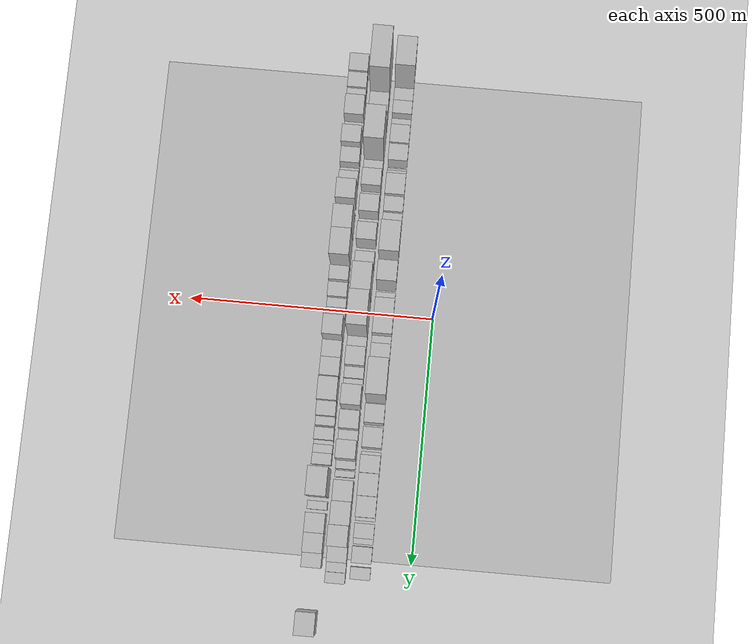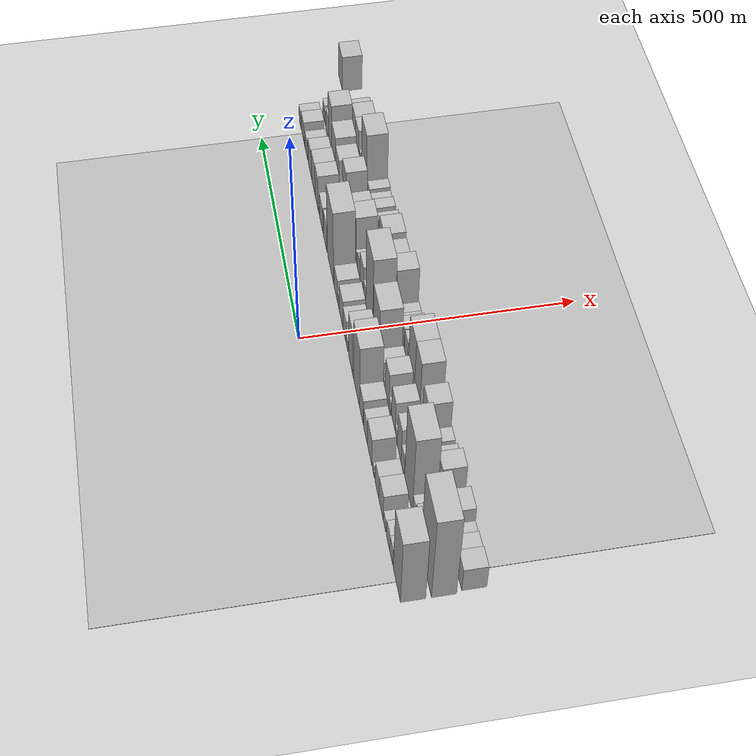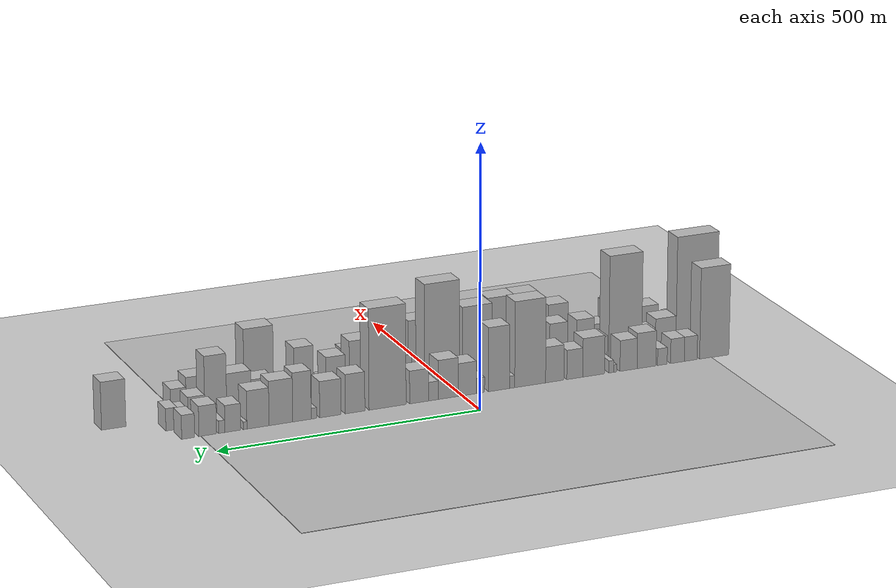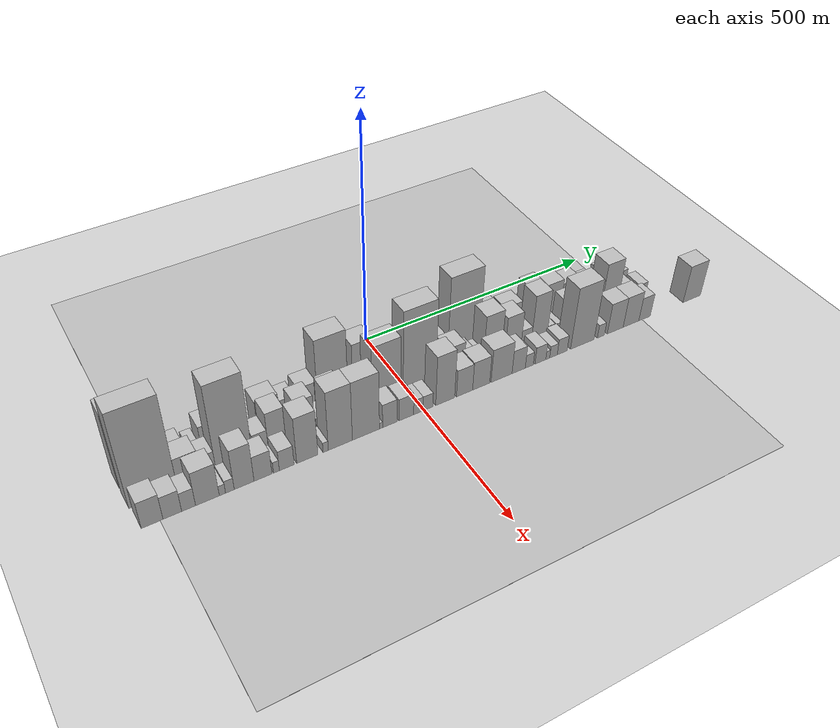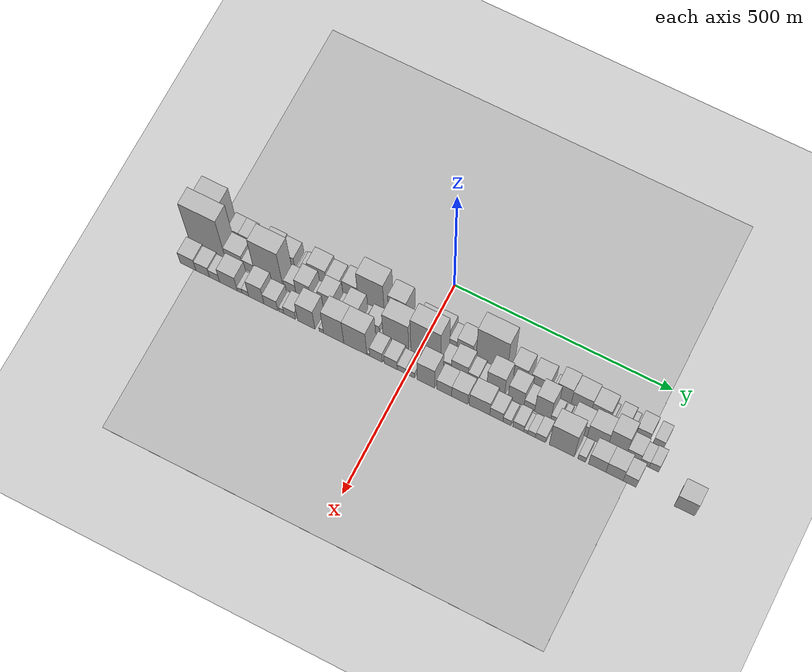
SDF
<?xml version="1.0" encoding="utf-8"?>

<sdf version="1.6">

   <world name="default">

      <gui fullscreen="0">

         <camera name="user_camera">

            <pose>-15 0 4.57585 0 0 0</pose>

            <view_controller>orbit</view_controller>

         </camera>

      </gui>

      <scene>

         <sky>

           <clouds>

             <speed>12</speed>

           </clouds>

         </sky>

         <ambient>0.4 0.4 0.4 1</ambient>

         <background>0.7 0.7 0.7 1</background>

         <shadows>1</shadows>

      </scene>

      <gravity>0 0 -9.8066</gravity>

      <magnetic_field>6e-06 2.3e-05 -4.2e-05</magnetic_field>

      <physics default="0" name="default_physics" type="ode">

         <ode>

            <solver>

               <type>quick</type>

               <iters>10</iters>

               <sor>1.0</sor>

               <use_dynamic_moi_rescaling>0</use_dynamic_moi_rescaling>

            </solver>

            <constraints>

               <cfm>0</cfm>

               <erp>0.2</erp>

               <contact_max_correcting_vel>100</contact_max_correcting_vel>

               <contact_surface_layer>0.001</contact_surface_layer>

            </constraints>

         </ode>

         <max_step_size>0.004</max_step_size>

         <real_time_factor>1</real_time_factor>

         <real_time_update_rate>250</real_time_update_rate>

      </physics>

      <light name="sun" type="directional">

         <cast_shadows>1</cast_shadows>

         <pose>0 0 10 0 0 0</pose>

         <diffuse>0.8 0.8 0.8 1</diffuse>

         <specular>0.2 0.2 0.2 1</specular>

         <attenuation>

            <range>1000</range>

            <constant>0.9</constant>

            <linear>0.01</linear>

            <quadratic>0.001</quadratic>

         </attenuation>

         <direction>-0.5 0.1 -0.9</direction>

      </light>

      <include>

         <name>ground_plane_1</name>

         <uri>model://HANNAS_ground_plane</uri>

         <pose>0 0 0  0 0 0</pose>

      </include>

      <include>

         <name>ground_plane_2</name>

         <uri>model://HANNAS_ground_plane</uri>

         <pose>100 0 0  0 0 0</pose>

      </include>

      <model name="building_1">

         <static>1</static>

         <pose frame="">100.0000 -505.8273 0 0.000000 0.000000 0.000000</pose>

         <link name="link">

            <pose frame="">0 0 88.50 0 0 0</pose>

            <collision name="collision">

               <geometry>

                  <box>

                     <size>40.0000 60.3455 177.0000</size>

                  </box>

               </geometry>

               <max_contacts>10</max_contacts>

               <surface>

                  <contact>

                     <ode/>

                  </contact>

                  <bounce/>

                  <friction>

                     <torsional>

                        <ode/>

                     </torsional>

                     <ode/>

                  </friction>

               </surface>

            </collision>

            <visual name="visual">

               <cast_shadows>0</cast_shadows>

               <geometry>

                  <box>

                     <size>40.0000 60.3455 177.0000</size>

                  </box>

               </geometry>

               <material>

                  <script>

                     <uri>model://HANNAS_wall/materials/scripts</uri>

                     <uri>model://HANNAS_wall/materials/textures</uri>

                     <name>vrc/HANNAS_wall</name>

                  </script>

               </material>

            </visual>

            <self_collide>0</self_collide>

            <enable_wind>0</enable_wind>

            <kinematic>0</kinematic>

         </link>

      </model>

      <model name="building_2">

         <static>1</static>

         <pose frame="">100.0000 -457.5397 0 0.000000 0.000000 0.000000</pose>

         <link name="link">

            <pose frame="">0 0 24.00 0 0 0</pose>

            <collision name="collision">

               <geometry>

                  <box>

                     <size>40.0000 26.2296 48.0000</size>

                  </box>

               </geometry>

               <max_contacts>10</max_contacts>

               <surface>

                  <contact>

                     <ode/>

                  </contact>

                  <bounce/>

                  <friction>

                     <torsional>

                        <ode/>

                     </torsional>

                     <ode/>

                  </friction>

               </surface>

            </collision>

            <visual name="visual">

               <cast_shadows>0</cast_shadows>

               <geometry>

                  <box>

                     <size>40.0000 26.2296 48.0000</size>

                  </box>

               </geometry>

               <material>

                  <script>

                     <uri>model://HANNAS_wall/materials/scripts</uri>

                     <uri>model://HANNAS_wall/materials/textures</uri>

                     <name>vrc/HANNAS_wall</name>

                  </script>

               </material>

            </visual>

            <self_collide>0</self_collide>

            <enable_wind>0</enable_wind>

            <kinematic>0</kinematic>

         </link>

      </model>

      <model name="building_3">

         <static>1</static>

         <pose frame="">100.0000 -430.3241 0 0.000000 0.000000 0.000000</pose>

         <link name="link">

            <pose frame="">0 0 24.00 0 0 0</pose>

            <collision name="collision">

               <geometry>

                  <box>

                     <size>40.0000 28.2017 48.0000</size>

                  </box>

               </geometry>

               <max_contacts>10</max_contacts>

               <surface>

                  <contact>

                     <ode/>

                  </contact>

                  <bounce/>

                  <friction>

                     <torsional>

                        <ode/>

                     </torsional>

                     <ode/>

                  </friction>

               </surface>

            </collision>

            <visual name="visual">

               <cast_shadows>0</cast_shadows>

               <geometry>

                  <box>

                     <size>40.0000 28.2017 48.0000</size>

                  </box>

               </geometry>

               <material>

                  <script>

                     <uri>model://HANNAS_wall/materials/scripts</uri>

                     <uri>model://HANNAS_wall/materials/textures</uri>

                     <name>vrc/HANNAS_wall</name>

                  </script>

               </material>

            </visual>

            <self_collide>0</self_collide>

            <enable_wind>0</enable_wind>

            <kinematic>0</kinematic>

         </link>

      </model>

      <model name="building_4">

         <static>1</static>

         <pose frame="">100.0000 -399.3763 0 0.000000 0.000000 0.000000</pose>

         <link name="link">

            <pose frame="">0 0 16.50 0 0 0</pose>

            <collision name="collision">

               <geometry>

                  <box>

                     <size>40.0000 19.6938 33.0000</size>

                  </box>

               </geometry>

               <max_contacts>10</max_contacts>

               <surface>

                  <contact>

                     <ode/>

                  </contact>

                  <bounce/>

                  <friction>

                     <torsional>

                        <ode/>

                     </torsional>

                     <ode/>

                  </friction>

               </surface>

            </collision>

            <visual name="visual">

               <cast_shadows>0</cast_shadows>

               <geometry>

                  <box>

                     <size>40.0000 19.6938 33.0000</size>

                  </box>

               </geometry>

               <material>

                  <script>

                     <uri>model://HANNAS_wall/materials/scripts</uri>

                     <uri>model://HANNAS_wall/materials/textures</uri>

                     <name>vrc/HANNAS_wall</name>

                  </script>

               </material>

            </visual>

            <self_collide>0</self_collide>

            <enable_wind>0</enable_wind>

            <kinematic>0</kinematic>

         </link>

      </model>

      <model name="building_5">

         <static>1</static>

         <pose frame="">100.0000 -367.3331 0 0.000000 0.000000 0.000000</pose>

         <link name="link">

            <pose frame="">0 0 34.50 0 0 0</pose>

            <collision name="collision">

               <geometry>

                  <box>

                     <size>40.0000 38.3928 69.0000</size>

                  </box>

               </geometry>

               <max_contacts>10</max_contacts>

               <surface>

                  <contact>

                     <ode/>

                  </contact>

                  <bounce/>

                  <friction>

                     <torsional>

                        <ode/>

                     </torsional>

                     <ode/>

                  </friction>

               </surface>

            </collision>

            <visual name="visual">

               <cast_shadows>0</cast_shadows>

               <geometry>

                  <box>

                     <size>40.0000 38.3928 69.0000</size>

                  </box>

               </geometry>

               <material>

                  <script>

                     <uri>model://HANNAS_wall/materials/scripts</uri>

                     <uri>model://HANNAS_wall/materials/textures</uri>

                     <name>vrc/HANNAS_wall</name>

                  </script>

               </material>

            </visual>

            <self_collide>0</self_collide>

            <enable_wind>0</enable_wind>

            <kinematic>0</kinematic>

         </link>

      </model>

      <model name="building_6">

         <static>1</static>

         <pose frame="">100.0000 -330.7315 0 0.000000 0.000000 0.000000</pose>

         <link name="link">

            <pose frame="">0 0 30.00 0 0 0</pose>

            <collision name="collision">

               <geometry>

                  <box>

                     <size>40.0000 34.8104 60.0000</size>

                  </box>

               </geometry>

               <max_contacts>10</max_contacts>

               <surface>

                  <contact>

                     <ode/>

                  </contact>

                  <bounce/>

                  <friction>

                     <torsional>

                        <ode/>

                     </torsional>

                     <ode/>

                  </friction>

               </surface>

            </collision>

            <visual name="visual">

               <cast_shadows>0</cast_shadows>

               <geometry>

                  <box>

                     <size>40.0000 34.8104 60.0000</size>

                  </box>

               </geometry>

               <material>

                  <script>

                     <uri>model://HANNAS_wall/materials/scripts</uri>

                     <uri>model://HANNAS_wall/materials/textures</uri>

                     <name>vrc/HANNAS_wall</name>

                  </script>

               </material>

            </visual>

            <self_collide>0</self_collide>

            <enable_wind>0</enable_wind>

            <kinematic>0</kinematic>

         </link>

      </model>

      <model name="building_7">

         <static>1</static>

         <pose frame="">100.0000 -304.1413 0 0.000000 0.000000 0.000000</pose>

         <link name="link">

            <pose frame="">0 0 7.50 0 0 0</pose>

            <collision name="collision">

               <geometry>

                  <box>

                     <size>40.0000 6.3700 15.0000</size>

                  </box>

               </geometry>

               <max_contacts>10</max_contacts>

               <surface>

                  <contact>

                     <ode/>

                  </contact>

                  <bounce/>

                  <friction>

                     <torsional>

                        <ode/>

                     </torsional>

                     <ode/>

                  </friction>

               </surface>

            </collision>

            <visual name="visual">

               <cast_shadows>0</cast_shadows>

               <geometry>

                  <box>

                     <size>40.0000 6.3700 15.0000</size>

                  </box>

               </geometry>

               <material>

                  <script>

                     <uri>model://HANNAS_wall/materials/scripts</uri>

                     <uri>model://HANNAS_wall/materials/textures</uri>

                     <name>vrc/HANNAS_wall</name>

                  </script>

               </material>

            </visual>

            <self_collide>0</self_collide>

            <enable_wind>0</enable_wind>

            <kinematic>0</kinematic>

         </link>

      </model>

      <model name="building_8">

         <static>1</static>

         <pose frame="">100.0000 -296.1098 0 0.000000 0.000000 0.000000</pose>

         <link name="link">

            <pose frame="">0 0 12.00 0 0 0</pose>

            <collision name="collision">

               <geometry>

                  <box>

                     <size>40.0000 9.6930 24.0000</size>

                  </box>

               </geometry>

               <max_contacts>10</max_contacts>

               <surface>

                  <contact>

                     <ode/>

                  </contact>

                  <bounce/>

                  <friction>

                     <torsional>

                        <ode/>

                     </torsional>

                     <ode/>

                  </friction>

               </surface>

            </collision>

            <visual name="visual">

               <cast_shadows>0</cast_shadows>

               <geometry>

                  <box>

                     <size>40.0000 9.6930 24.0000</size>

                  </box>

               </geometry>

               <material>

                  <script>

                     <uri>model://HANNAS_wall/materials/scripts</uri>

                     <uri>model://HANNAS_wall/materials/textures</uri>

                     <name>vrc/HANNAS_wall</name>

                  </script>

               </material>

            </visual>

            <self_collide>0</self_collide>

            <enable_wind>0</enable_wind>

            <kinematic>0</kinematic>

         </link>

      </model>

      <model name="building_9">

         <static>1</static>

         <pose frame="">100.0000 -260.4263 0 0.000000 0.000000 0.000000</pose>

         <link name="link">

            <pose frame="">0 0 37.50 0 0 0</pose>

            <collision name="collision">

               <geometry>

                  <box>

                     <size>40.0000 43.6740 75.0000</size>

                  </box>

               </geometry>

               <max_contacts>10</max_contacts>

               <surface>

                  <contact>

                     <ode/>

                  </contact>

                  <bounce/>

                  <friction>

                     <torsional>

                        <ode/>

                     </torsional>

                     <ode/>

                  </friction>

               </surface>

            </collision>

            <visual name="visual">

               <cast_shadows>0</cast_shadows>

               <geometry>

                  <box>

                     <size>40.0000 43.6740 75.0000</size>

                  </box>

               </geometry>

               <material>

                  <script>

                     <uri>model://HANNAS_wall/materials/scripts</uri>

                     <uri>model://HANNAS_wall/materials/textures</uri>

                     <name>vrc/HANNAS_wall</name>

                  </script>

               </material>

            </visual>

            <self_collide>0</self_collide>

            <enable_wind>0</enable_wind>

            <kinematic>0</kinematic>

         </link>

      </model>

      <model name="building_10">

         <static>1</static>

         <pose frame="">100.0000 -222.5610 0 0.000000 0.000000 0.000000</pose>

         <link name="link">

            <pose frame="">0 0 28.50 0 0 0</pose>

            <collision name="collision">

               <geometry>

                  <box>

                     <size>40.0000 32.0565 57.0000</size>

                  </box>

               </geometry>

               <max_contacts>10</max_contacts>

               <surface>

                  <contact>

                     <ode/>

                  </contact>

                  <bounce/>

                  <friction>

                     <torsional>

                        <ode/>

                     </torsional>

                     <ode/>

                  </friction>

               </surface>

            </collision>

            <visual name="visual">

               <cast_shadows>0</cast_shadows>

               <geometry>

                  <box>

                     <size>40.0000 32.0565 57.0000</size>

                  </box>

               </geometry>

               <material>

                  <script>

                     <uri>model://HANNAS_wall/materials/scripts</uri>

                     <uri>model://HANNAS_wall/materials/textures</uri>

                     <name>vrc/HANNAS_wall</name>

                  </script>

               </material>

            </visual>

            <self_collide>0</self_collide>

            <enable_wind>0</enable_wind>

            <kinematic>0</kinematic>

         </link>

      </model>

      <model name="building_11">

         <static>1</static>

         <pose frame="">100.0000 -182.3445 0 0.000000 0.000000 0.000000</pose>

         <link name="link">

            <pose frame="">0 0 34.50 0 0 0</pose>

            <collision name="collision">

               <geometry>

                  <box>

                     <size>40.0000 36.3766 69.0000</size>

                  </box>

               </geometry>

               <max_contacts>10</max_contacts>

               <surface>

                  <contact>

                     <ode/>

                  </contact>

                  <bounce/>

                  <friction>

                     <torsional>

                        <ode/>

                     </torsional>

                     <ode/>

                  </friction>

               </surface>

            </collision>

            <visual name="visual">

               <cast_shadows>0</cast_shadows>

               <geometry>

                  <box>

                     <size>40.0000 36.3766 69.0000</size>

                  </box>

               </geometry>

               <material>

                  <script>

                     <uri>model://HANNAS_wall/materials/scripts</uri>

                     <uri>model://HANNAS_wall/materials/textures</uri>

                     <name>vrc/HANNAS_wall</name>

                  </script>

               </material>

            </visual>

            <self_collide>0</self_collide>

            <enable_wind>0</enable_wind>

            <kinematic>0</kinematic>

         </link>

      </model>

      <model name="building_12">

         <static>1</static>

         <pose frame="">100.0000 -133.5054 0 0.000000 0.000000 0.000000</pose>

         <link name="link">

            <pose frame="">0 0 82.50 0 0 0</pose>

            <collision name="collision">

               <geometry>

                  <box>

                     <size>40.0000 61.3015 165.0000</size>

                  </box>

               </geometry>

               <max_contacts>10</max_contacts>

               <surface>

                  <contact>

                     <ode/>

                  </contact>

                  <bounce/>

                  <friction>

                     <torsional>

                        <ode/>

                     </torsional>

                     <ode/>

                  </friction>

               </surface>

            </collision>

            <visual name="visual">

               <cast_shadows>0</cast_shadows>

               <geometry>

                  <box>

                     <size>40.0000 61.3015 165.0000</size>

                  </box>

               </geometry>

               <material>

                  <script>

                     <uri>model://HANNAS_wall/materials/scripts</uri>

                     <uri>model://HANNAS_wall/materials/textures</uri>

                     <name>vrc/HANNAS_wall</name>

                  </script>

               </material>

            </visual>

            <self_collide>0</self_collide>

            <enable_wind>0</enable_wind>

            <kinematic>0</kinematic>

         </link>

      </model>

      <model name="building_13">

         <static>1</static>

         <pose frame="">100.0000 -97.8086 0 0.000000 0.000000 0.000000</pose>

         <link name="link">

            <pose frame="">0 0 12.00 0 0 0</pose>

            <collision name="collision">

               <geometry>

                  <box>

                     <size>40.0000 10.0921 24.0000</size>

                  </box>

               </geometry>

               <max_contacts>10</max_contacts>

               <surface>

                  <contact>

                     <ode/>

                  </contact>

                  <bounce/>

                  <friction>

                     <torsional>

                        <ode/>

                     </torsional>

                     <ode/>

                  </friction>

               </surface>

            </collision>

            <visual name="visual">

               <cast_shadows>0</cast_shadows>

               <geometry>

                  <box>

                     <size>40.0000 10.0921 24.0000</size>

                  </box>

               </geometry>

               <material>

                  <script>

                     <uri>model://HANNAS_wall/materials/scripts</uri>

                     <uri>model://HANNAS_wall/materials/textures</uri>

                     <name>vrc/HANNAS_wall</name>

                  </script>

               </material>

            </visual>

            <self_collide>0</self_collide>

            <enable_wind>0</enable_wind>

            <kinematic>0</kinematic>

         </link>

      </model>

      <model name="building_14">

         <static>1</static>

         <pose frame="">100.0000 -72.0178 0 0.000000 0.000000 0.000000</pose>

         <link name="link">

            <pose frame="">0 0 61.50 0 0 0</pose>

            <collision name="collision">

               <geometry>

                  <box>

                     <size>40.0000 41.4896 123.0000</size>

                  </box>

               </geometry>

               <max_contacts>10</max_contacts>

               <surface>

                  <contact>

                     <ode/>

                  </contact>

                  <bounce/>

                  <friction>

                     <torsional>

                        <ode/>

                     </torsional>

                     <ode/>

                  </friction>

               </surface>

            </collision>

            <visual name="visual">

               <cast_shadows>0</cast_shadows>

               <geometry>

                  <box>

                     <size>40.0000 41.4896 123.0000</size>

                  </box>

               </geometry>

               <material>

                  <script>

                     <uri>model://HANNAS_wall/materials/scripts</uri>

                     <uri>model://HANNAS_wall/materials/textures</uri>

                     <name>vrc/HANNAS_wall</name>

                  </script>

               </material>

            </visual>

            <self_collide>0</self_collide>

            <enable_wind>0</enable_wind>

            <kinematic>0</kinematic>

         </link>

      </model>

      <model name="building_15">

         <static>1</static>

         <pose frame="">100.0000 -35.1359 0 0.000000 0.000000 0.000000</pose>

         <link name="link">

            <pose frame="">0 0 15.00 0 0 0</pose>

            <collision name="collision">

               <geometry>

                  <box>

                     <size>40.0000 16.2741 30.0000</size>

                  </box>

               </geometry>

               <max_contacts>10</max_contacts>

               <surface>

                  <contact>

                     <ode/>

                  </contact>

                  <bounce/>

                  <friction>

                     <torsional>

                        <ode/>

                     </torsional>

                     <ode/>

                  </friction>

               </surface>

            </collision>

            <visual name="visual">

               <cast_shadows>0</cast_shadows>

               <geometry>

                  <box>

                     <size>40.0000 16.2741 30.0000</size>

                  </box>

               </geometry>

               <material>

                  <script>

                     <uri>model://HANNAS_wall/materials/scripts</uri>

                     <uri>model://HANNAS_wall/materials/textures</uri>

                     <name>vrc/HANNAS_wall</name>

                  </script>

               </material>

            </visual>

            <self_collide>0</self_collide>

            <enable_wind>0</enable_wind>

            <kinematic>0</kinematic>

         </link>

      </model>

      <model name="building_16">

         <static>1</static>

         <pose frame="">100.0000 -9.4625 0 0.000000 0.000000 0.000000</pose>

         <link name="link">

            <pose frame="">0 0 31.50 0 0 0</pose>

            <collision name="collision">

               <geometry>

                  <box>

                     <size>40.0000 35.0727 63.0000</size>

                  </box>

               </geometry>

               <max_contacts>10</max_contacts>

               <surface>

                  <contact>

                     <ode/>

                  </contact>

                  <bounce/>

                  <friction>

                     <torsional>

                        <ode/>

                     </torsional>

                     <ode/>

                  </friction>

               </surface>

            </collision>

            <visual name="visual">

               <cast_shadows>0</cast_shadows>

               <geometry>

                  <box>

                     <size>40.0000 35.0727 63.0000</size>

                  </box>

               </geometry>

               <material>

                  <script>

                     <uri>model://HANNAS_wall/materials/scripts</uri>

                     <uri>model://HANNAS_wall/materials/textures</uri>

                     <name>vrc/HANNAS_wall</name>

                  </script>

               </material>

            </visual>

            <self_collide>0</self_collide>

            <enable_wind>0</enable_wind>

            <kinematic>0</kinematic>

         </link>

      </model>

      <model name="building_17">

         <static>1</static>

         <pose frame="">100.0000 27.9538 0 0.000000 0.000000 0.000000</pose>

         <link name="link">

            <pose frame="">0 0 37.50 0 0 0</pose>

            <collision name="collision">

               <geometry>

                  <box>

                     <size>40.0000 39.7601 75.0000</size>

                  </box>

               </geometry>

               <max_contacts>10</max_contacts>

               <surface>

                  <contact>

                     <ode/>

                  </contact>

                  <bounce/>

                  <friction>

                     <torsional>

                        <ode/>

                     </torsional>

                     <ode/>

                  </friction>

               </surface>

            </collision>

            <visual name="visual">

               <cast_shadows>0</cast_shadows>

               <geometry>

                  <box>

                     <size>40.0000 39.7601 75.0000</size>

                  </box>

               </geometry>

               <material>

                  <script>

                     <uri>model://HANNAS_wall/materials/scripts</uri>

                     <uri>model://HANNAS_wall/materials/textures</uri>

                     <name>vrc/HANNAS_wall</name>

                  </script>

               </material>

            </visual>

            <self_collide>0</self_collide>

            <enable_wind>0</enable_wind>

            <kinematic>0</kinematic>

         </link>

      </model>

      <model name="building_18">

         <static>1</static>

         <pose frame="">100.0000 57.0357 0 0.000000 0.000000 0.000000</pose>

         <link name="link">

            <pose frame="">0 0 18.00 0 0 0</pose>

            <collision name="collision">

               <geometry>

                  <box>

                     <size>40.0000 18.4037 36.0000</size>

                  </box>

               </geometry>

               <max_contacts>10</max_contacts>

               <surface>

                  <contact>

                     <ode/>

                  </contact>

                  <bounce/>

                  <friction>

                     <torsional>

                        <ode/>

                     </torsional>

                     <ode/>

                  </friction>

               </surface>

            </collision>

            <visual name="visual">

               <cast_shadows>0</cast_shadows>

               <geometry>

                  <box>

                     <size>40.0000 18.4037 36.0000</size>

                  </box>

               </geometry>

               <material>

                  <script>

                     <uri>model://HANNAS_wall/materials/scripts</uri>

                     <uri>model://HANNAS_wall/materials/textures</uri>

                     <name>vrc/HANNAS_wall</name>

                  </script>

               </material>

            </visual>

            <self_collide>0</self_collide>

            <enable_wind>0</enable_wind>

            <kinematic>0</kinematic>

         </link>

      </model>

      <model name="building_19">

         <static>1</static>

         <pose frame="">100.0000 84.7148 0 0.000000 0.000000 0.000000</pose>

         <link name="link">

            <pose frame="">0 0 31.50 0 0 0</pose>

            <collision name="collision">

               <geometry>

                  <box>

                     <size>40.0000 36.9546 63.0000</size>

                  </box>

               </geometry>

               <max_contacts>10</max_contacts>

               <surface>

                  <contact>

                     <ode/>

                  </contact>

                  <bounce/>

                  <friction>

                     <torsional>

                        <ode/>

                     </torsional>

                     <ode/>

                  </friction>

               </surface>

            </collision>

            <visual name="visual">

               <cast_shadows>0</cast_shadows>

               <geometry>

                  <box>

                     <size>40.0000 36.9546 63.0000</size>

                  </box>

               </geometry>

               <material>

                  <script>

                     <uri>model://HANNAS_wall/materials/scripts</uri>

                     <uri>model://HANNAS_wall/materials/textures</uri>

                     <name>vrc/HANNAS_wall</name>

                  </script>

               </material>

            </visual>

            <self_collide>0</self_collide>

            <enable_wind>0</enable_wind>

            <kinematic>0</kinematic>

         </link>

      </model>

      <model name="building_20">

         <static>1</static>

         <pose frame="">100.0000 145.9406 0 0.000000 0.000000 0.000000</pose>

         <link name="link">

            <pose frame="">0 0 96.00 0 0 0</pose>

            <collision name="collision">

               <geometry>

                  <box>

                     <size>40.0000 71.4970 192.0000</size>

                  </box>

               </geometry>

               <max_contacts>10</max_contacts>

               <surface>

                  <contact>

                     <ode/>

                  </contact>

                  <bounce/>

                  <friction>

                     <torsional>

                        <ode/>

                     </torsional>

                     <ode/>

                  </friction>

               </surface>

            </collision>

            <visual name="visual">

               <cast_shadows>0</cast_shadows>

               <geometry>

                  <box>

                     <size>40.0000 71.4970 192.0000</size>

                  </box>

               </geometry>

               <material>

                  <script>

                     <uri>model://HANNAS_wall/materials/scripts</uri>

                     <uri>model://HANNAS_wall/materials/textures</uri>

                     <name>vrc/HANNAS_wall</name>

                  </script>

               </material>

            </visual>

            <self_collide>0</self_collide>

            <enable_wind>0</enable_wind>

            <kinematic>0</kinematic>

         </link>

      </model>

      <model name="building_21">

         <static>1</static>

         <pose frame="">100.0000 208.5937 0 0.000000 0.000000 0.000000</pose>

         <link name="link">

            <pose frame="">0 0 37.50 0 0 0</pose>

            <collision name="collision">

               <geometry>

                  <box>

                     <size>40.0000 37.8092 75.0000</size>

                  </box>

               </geometry>

               <max_contacts>10</max_contacts>

               <surface>

                  <contact>

                     <ode/>

                  </contact>

                  <bounce/>

                  <friction>

                     <torsional>

                        <ode/>

                     </torsional>

                     <ode/>

                  </friction>

               </surface>

            </collision>

            <visual name="visual">

               <cast_shadows>0</cast_shadows>

               <geometry>

                  <box>

                     <size>40.0000 37.8092 75.0000</size>

                  </box>

               </geometry>

               <material>

                  <script>

                     <uri>model://HANNAS_wall/materials/scripts</uri>

                     <uri>model://HANNAS_wall/materials/textures</uri>

                     <name>vrc/HANNAS_wall</name>

                  </script>

               </material>

            </visual>

            <self_collide>0</self_collide>

            <enable_wind>0</enable_wind>

            <kinematic>0</kinematic>

         </link>

      </model>

      <model name="building_22">

         <static>1</static>

         <pose frame="">100.0000 255.8856 0 0.000000 0.000000 0.000000</pose>

         <link name="link">

            <pose frame="">0 0 34.50 0 0 0</pose>

            <collision name="collision">

               <geometry>

                  <box>

                     <size>40.0000 40.7748 69.0000</size>

                  </box>

               </geometry>

               <max_contacts>10</max_contacts>

               <surface>

                  <contact>

                     <ode/>

                  </contact>

                  <bounce/>

                  <friction>

                     <torsional>

                        <ode/>

                     </torsional>

                     <ode/>

                  </friction>

               </surface>

            </collision>

            <visual name="visual">

               <cast_shadows>0</cast_shadows>

               <geometry>

                  <box>

                     <size>40.0000 40.7748 69.0000</size>

                  </box>

               </geometry>

               <material>

                  <script>

                     <uri>model://HANNAS_wall/materials/scripts</uri>

                     <uri>model://HANNAS_wall/materials/textures</uri>

                     <name>vrc/HANNAS_wall</name>

                  </script>

               </material>

            </visual>

            <self_collide>0</self_collide>

            <enable_wind>0</enable_wind>

            <kinematic>0</kinematic>

         </link>

      </model>

      <model name="building_23">

         <static>1</static>

         <pose frame="">100.0000 287.3628 0 0.000000 0.000000 0.000000</pose>

         <link name="link">

            <pose frame="">0 0 10.50 0 0 0</pose>

            <collision name="collision">

               <geometry>

                  <box>

                     <size>40.0000 10.1794 21.0000</size>

                  </box>

               </geometry>

               <max_contacts>10</max_contacts>

               <surface>

                  <contact>

                     <ode/>

                  </contact>

                  <bounce/>

                  <friction>

                     <torsional>

                        <ode/>

                     </torsional>

                     <ode/>

                  </friction>

               </surface>

            </collision>

            <visual name="visual">

               <cast_shadows>0</cast_shadows>

               <geometry>

                  <box>

                     <size>40.0000 10.1794 21.0000</size>

                  </box>

               </geometry>

               <material>

                  <script>

                     <uri>model://HANNAS_wall/materials/scripts</uri>

                     <uri>model://HANNAS_wall/materials/textures</uri>

                     <name>vrc/HANNAS_wall</name>

                  </script>

               </material>

            </visual>

            <self_collide>0</self_collide>

            <enable_wind>0</enable_wind>

            <kinematic>0</kinematic>

         </link>

      </model>

      <model name="building_24">

         <static>1</static>

         <pose frame="">100.0000 309.9625 0 0.000000 0.000000 0.000000</pose>

         <link name="link">

            <pose frame="">0 0 46.50 0 0 0</pose>

            <collision name="collision">

               <geometry>

                  <box>

                     <size>40.0000 35.0200 93.0000</size>

                  </box>

               </geometry>

               <max_contacts>10</max_contacts>

               <surface>

                  <contact>

                     <ode/>

                  </contact>

                  <bounce/>

                  <friction>

                     <torsional>

                        <ode/>

                     </torsional>

                     <ode/>

                  </friction>

               </surface>

            </collision>

            <visual name="visual">

               <cast_shadows>0</cast_shadows>

               <geometry>

                  <box>

                     <size>40.0000 35.0200 93.0000</size>

                  </box>

               </geometry>

               <material>

                  <script>

                     <uri>model://HANNAS_wall/materials/scripts</uri>

                     <uri>model://HANNAS_wall/materials/textures</uri>

                     <name>vrc/HANNAS_wall</name>

                  </script>

               </material>

            </visual>

            <self_collide>0</self_collide>

            <enable_wind>0</enable_wind>

            <kinematic>0</kinematic>

         </link>

      </model>

      <model name="building_25">

         <static>1</static>

         <pose frame="">100.0000 349.8881 0 0.000000 0.000000 0.000000</pose>

         <link name="link">

            <pose frame="">0 0 42.00 0 0 0</pose>

            <collision name="collision">

               <geometry>

                  <box>

                     <size>40.0000 44.8312 84.0000</size>

                  </box>

               </geometry>

               <max_contacts>10</max_contacts>

               <surface>

                  <contact>

                     <ode/>

                  </contact>

                  <bounce/>

                  <friction>

                     <torsional>

                        <ode/>

                     </torsional>

                     <ode/>

                  </friction>

               </surface>

            </collision>

            <visual name="visual">

               <cast_shadows>0</cast_shadows>

               <geometry>

                  <box>

                     <size>40.0000 44.8312 84.0000</size>

                  </box>

               </geometry>

               <material>

                  <script>

                     <uri>model://HANNAS_wall/materials/scripts</uri>

                     <uri>model://HANNAS_wall/materials/textures</uri>

                     <name>vrc/HANNAS_wall</name>

                  </script>

               </material>

            </visual>

            <self_collide>0</self_collide>

            <enable_wind>0</enable_wind>

            <kinematic>0</kinematic>

         </link>

      </model>

      <model name="building_26">

         <static>1</static>

         <pose frame="">100.0000 393.1791 0 0.000000 0.000000 0.000000</pose>

         <link name="link">

            <pose frame="">0 0 36.00 0 0 0</pose>

            <collision name="collision">

               <geometry>

                  <box>

                     <size>40.0000 41.7509 72.0000</size>

                  </box>

               </geometry>

               <max_contacts>10</max_contacts>

               <surface>

                  <contact>

                     <ode/>

                  </contact>

                  <bounce/>

                  <friction>

                     <torsional>

                        <ode/>

                     </torsional>

                     <ode/>

                  </friction>

               </surface>

            </collision>

            <visual name="visual">

               <cast_shadows>0</cast_shadows>

               <geometry>

                  <box>

                     <size>40.0000 41.7509 72.0000</size>

                  </box>

               </geometry>

               <material>

                  <script>

                     <uri>model://HANNAS_wall/materials/scripts</uri>

                     <uri>model://HANNAS_wall/materials/textures</uri>

                     <name>vrc/HANNAS_wall</name>

                  </script>

               </material>

            </visual>

            <self_collide>0</self_collide>

            <enable_wind>0</enable_wind>

            <kinematic>0</kinematic>

         </link>

      </model>

      <model name="building_27">

         <static>1</static>

         <pose frame="">100.0000 417.5110 0 0.000000 0.000000 0.000000</pose>

         <link name="link">

            <pose frame="">0 0 7.50 0 0 0</pose>

            <collision name="collision">

               <geometry>

                  <box>

                     <size>40.0000 6.9128 15.0000</size>

                  </box>

               </geometry>

               <max_contacts>10</max_contacts>

               <surface>

                  <contact>

                     <ode/>

                  </contact>

                  <bounce/>

                  <friction>

                     <torsional>

                        <ode/>

                     </torsional>

                     <ode/>

                  </friction>

               </surface>

            </collision>

            <visual name="visual">

               <cast_shadows>0</cast_shadows>

               <geometry>

                  <box>

                     <size>40.0000 6.9128 15.0000</size>

                  </box>

               </geometry>

               <material>

                  <script>

                     <uri>model://HANNAS_wall/materials/scripts</uri>

                     <uri>model://HANNAS_wall/materials/textures</uri>

                     <name>vrc/HANNAS_wall</name>

                  </script>

               </material>

            </visual>

            <self_collide>0</self_collide>

            <enable_wind>0</enable_wind>

            <kinematic>0</kinematic>

         </link>

      </model>

      <model name="building_28">

         <static>1</static>

         <pose frame="">100.0000 440.7020 0 0.000000 0.000000 0.000000</pose>

         <link name="link">

            <pose frame="">0 0 25.50 0 0 0</pose>

            <collision name="collision">

               <geometry>

                  <box>

                     <size>40.0000 29.4691 51.0000</size>

                  </box>

               </geometry>

               <max_contacts>10</max_contacts>

               <surface>

                  <contact>

                     <ode/>

                  </contact>

                  <bounce/>

                  <friction>

                     <torsional>

                        <ode/>

                     </torsional>

                     <ode/>

                  </friction>

               </surface>

            </collision>

            <visual name="visual">

               <cast_shadows>0</cast_shadows>

               <geometry>

                  <box>

                     <size>40.0000 29.4691 51.0000</size>

                  </box>

               </geometry>

               <material>

                  <script>

                     <uri>model://HANNAS_wall/materials/scripts</uri>

                     <uri>model://HANNAS_wall/materials/textures</uri>

                     <name>vrc/HANNAS_wall</name>

                  </script>

               </material>

            </visual>

            <self_collide>0</self_collide>

            <enable_wind>0</enable_wind>

            <kinematic>0</kinematic>

         </link>

      </model>

      <model name="building_29">

         <static>1</static>

         <pose frame="">100.0000 461.3419 0 0.000000 0.000000 0.000000</pose>

         <link name="link">

            <pose frame="">0 0 12.00 0 0 0</pose>

            <collision name="collision">

               <geometry>

                  <box>

                     <size>40.0000 11.8106 24.0000</size>

                  </box>

               </geometry>

               <max_contacts>10</max_contacts>

               <surface>

                  <contact>

                     <ode/>

                  </contact>

                  <bounce/>

                  <friction>

                     <torsional>

                        <ode/>

                     </torsional>

                     <ode/>

                  </friction>

               </surface>

            </collision>

            <visual name="visual">

               <cast_shadows>0</cast_shadows>

               <geometry>

                  <box>

                     <size>40.0000 11.8106 24.0000</size>

                  </box>

               </geometry>

               <material>

                  <script>

                     <uri>model://HANNAS_wall/materials/scripts</uri>

                     <uri>model://HANNAS_wall/materials/textures</uri>

                     <name>vrc/HANNAS_wall</name>

                  </script>

               </material>

            </visual>

            <self_collide>0</self_collide>

            <enable_wind>0</enable_wind>

            <kinematic>0</kinematic>

         </link>

      </model>

      <model name="building_30">

         <static>1</static>

         <pose frame="">100.0000 487.6232 0 0.000000 0.000000 0.000000</pose>

         <link name="link">

            <pose frame="">0 0 28.50 0 0 0</pose>

            <collision name="collision">

               <geometry>

                  <box>

                     <size>40.0000 32.7519 57.0000</size>

                  </box>

               </geometry>

               <max_contacts>10</max_contacts>

               <surface>

                  <contact>

                     <ode/>

                  </contact>

                  <bounce/>

                  <friction>

                     <torsional>

                        <ode/>

                     </torsional>

                     <ode/>

                  </friction>

               </surface>

            </collision>

            <visual name="visual">

               <cast_shadows>0</cast_shadows>

               <geometry>

                  <box>

                     <size>40.0000 32.7519 57.0000</size>

                  </box>

               </geometry>

               <material>

                  <script>

                     <uri>model://HANNAS_wall/materials/scripts</uri>

                     <uri>model://HANNAS_wall/materials/textures</uri>

                     <name>vrc/HANNAS_wall</name>

                  </script>

               </material>

            </visual>

            <self_collide>0</self_collide>

            <enable_wind>0</enable_wind>

            <kinematic>0</kinematic>

         </link>

      </model>

      <model name="building_31">

         <static>1</static>

         <pose frame="">100.0000 524.0731 0 0.000000 0.000000 0.000000</pose>

         <link name="link">

            <pose frame="">0 0 22.50 0 0 0</pose>

            <collision name="collision">

               <geometry>

                  <box>

                     <size>40.0000 24.1480 45.0000</size>

                  </box>

               </geometry>

               <max_contacts>10</max_contacts>

               <surface>

                  <contact>

                     <ode/>

                  </contact>

                  <bounce/>

                  <friction>

                     <torsional>

                        <ode/>

                     </torsional>

                     <ode/>

                  </friction>

               </surface>

            </collision>

            <visual name="visual">

               <cast_shadows>0</cast_shadows>

               <geometry>

                  <box>

                     <size>40.0000 24.1480 45.0000</size>

                  </box>

               </geometry>

               <material>

                  <script>

                     <uri>model://HANNAS_wall/materials/scripts</uri>

                     <uri>model://HANNAS_wall/materials/textures</uri>

                     <name>vrc/HANNAS_wall</name>

                  </script>

               </material>

            </visual>

            <self_collide>0</self_collide>

            <enable_wind>0</enable_wind>

            <kinematic>0</kinematic>

         </link>

      </model>

      <model name="building_32">

         <static>1</static>

         <pose frame="">149.0000 -493.4591 0 0.000000 0.000000 0.000000</pose>

         <link name="link">

            <pose frame="">0 0 112.50 0 0 0</pose>

            <collision name="collision">

               <geometry>

                  <box>

                     <size>40.0000 85.0817 225.0000</size>

                  </box>

               </geometry>

               <max_contacts>10</max_contacts>

               <surface>

                  <contact>

                     <ode/>

                  </contact>

                  <bounce/>

                  <friction>

                     <torsional>

                        <ode/>

                     </torsional>

                     <ode/>

                  </friction>

               </surface>

            </collision>

            <visual name="visual">

               <cast_shadows>0</cast_shadows>

               <geometry>

                  <box>

                     <size>40.0000 85.0817 225.0000</size>

                  </box>

               </geometry>

               <material>

                  <script>

                     <uri>model://HANNAS_wall/materials/scripts</uri>

                     <uri>model://HANNAS_wall/materials/textures</uri>

                     <name>vrc/HANNAS_wall</name>

                  </script>

               </material>

            </visual>

            <self_collide>0</self_collide>

            <enable_wind>0</enable_wind>

            <kinematic>0</kinematic>

         </link>

      </model>

      <model name="building_33">

         <static>1</static>

         <pose frame="">149.0000 -429.9121 0 0.000000 0.000000 0.000000</pose>

         <link name="link">

            <pose frame="">0 0 36.00 0 0 0</pose>

            <collision name="collision">

               <geometry>

                  <box>

                     <size>40.0000 42.0123 72.0000</size>

                  </box>

               </geometry>

               <max_contacts>10</max_contacts>

               <surface>

                  <contact>

                     <ode/>

                  </contact>

                  <bounce/>

                  <friction>

                     <torsional>

                        <ode/>

                     </torsional>

                     <ode/>

                  </friction>

               </surface>

            </collision>

            <visual name="visual">

               <cast_shadows>0</cast_shadows>

               <geometry>

                  <box>

                     <size>40.0000 42.0123 72.0000</size>

                  </box>

               </geometry>

               <material>

                  <script>

                     <uri>model://HANNAS_wall/materials/scripts</uri>

                     <uri>model://HANNAS_wall/materials/textures</uri>

                     <name>vrc/HANNAS_wall</name>

                  </script>

               </material>

            </visual>

            <self_collide>0</self_collide>

            <enable_wind>0</enable_wind>

            <kinematic>0</kinematic>

         </link>

      </model>

      <model name="building_34">

         <static>1</static>

         <pose frame="">149.0000 -394.9662 0 0.000000 0.000000 0.000000</pose>

         <link name="link">

            <pose frame="">0 0 27.00 0 0 0</pose>

            <collision name="collision">

               <geometry>

                  <box>

                     <size>40.0000 27.8796 54.0000</size>

                  </box>

               </geometry>

               <max_contacts>10</max_contacts>

               <surface>

                  <contact>

                     <ode/>

                  </contact>

                  <bounce/>

                  <friction>

                     <torsional>

                        <ode/>

                     </torsional>

                     <ode/>

                  </friction>

               </surface>

            </collision>

            <visual name="visual">

               <cast_shadows>0</cast_shadows>

               <geometry>

                  <box>

                     <size>40.0000 27.8796 54.0000</size>

                  </box>

               </geometry>

               <material>

                  <script>

                     <uri>model://HANNAS_wall/materials/scripts</uri>

                     <uri>model://HANNAS_wall/materials/textures</uri>

                     <name>vrc/HANNAS_wall</name>

                  </script>

               </material>

            </visual>

            <self_collide>0</self_collide>

            <enable_wind>0</enable_wind>

            <kinematic>0</kinematic>

         </link>

      </model>

      <model name="building_35">

         <static>1</static>

         <pose frame="">149.0000 -347.5158 0 0.000000 0.000000 0.000000</pose>

         <link name="link">

            <pose frame="">0 0 103.50 0 0 0</pose>

            <collision name="collision">

               <geometry>

                  <box>

                     <size>40.0000 67.0213 207.0000</size>

                  </box>

               </geometry>

               <max_contacts>10</max_contacts>

               <surface>

                  <contact>

                     <ode/>

                  </contact>

                  <bounce/>

                  <friction>

                     <torsional>

                        <ode/>

                     </torsional>

                     <ode/>

                  </friction>

               </surface>

            </collision>

            <visual name="visual">

               <cast_shadows>0</cast_shadows>

               <geometry>

                  <box>

                     <size>40.0000 67.0213 207.0000</size>

                  </box>

               </geometry>

               <material>

                  <script>

                     <uri>model://HANNAS_wall/materials/scripts</uri>

                     <uri>model://HANNAS_wall/materials/textures</uri>

                     <name>vrc/HANNAS_wall</name>

                  </script>

               </material>

            </visual>

            <self_collide>0</self_collide>

            <enable_wind>0</enable_wind>

            <kinematic>0</kinematic>

         </link>

      </model>

      <model name="building_36">

         <static>1</static>

         <pose frame="">149.0000 -297.4360 0 0.000000 0.000000 0.000000</pose>

         <link name="link">

            <pose frame="">0 0 27.00 0 0 0</pose>

            <collision name="collision">

               <geometry>

                  <box>

                     <size>40.0000 27.1383 54.0000</size>

                  </box>

               </geometry>

               <max_contacts>10</max_contacts>

               <surface>

                  <contact>

                     <ode/>

                  </contact>

                  <bounce/>

                  <friction>

                     <torsional>

                        <ode/>

                     </torsional>

                     <ode/>

                  </friction>

               </surface>

            </collision>

            <visual name="visual">

               <cast_shadows>0</cast_shadows>

               <geometry>

                  <box>

                     <size>40.0000 27.1383 54.0000</size>

                  </box>

               </geometry>

               <material>

                  <script>

                     <uri>model://HANNAS_wall/materials/scripts</uri>

                     <uri>model://HANNAS_wall/materials/textures</uri>

                     <name>vrc/HANNAS_wall</name>

                  </script>

               </material>

            </visual>

            <self_collide>0</self_collide>

            <enable_wind>0</enable_wind>

            <kinematic>0</kinematic>

         </link>

      </model>

      <model name="building_37">

         <static>1</static>

         <pose frame="">149.0000 -266.2538 0 0.000000 0.000000 0.000000</pose>

         <link name="link">

            <pose frame="">0 0 46.50 0 0 0</pose>

            <collision name="collision">

               <geometry>

                  <box>

                     <size>40.0000 35.2261 93.0000</size>

                  </box>

               </geometry>

               <max_contacts>10</max_contacts>

               <surface>

                  <contact>

                     <ode/>

                  </contact>

                  <bounce/>

                  <friction>

                     <torsional>

                        <ode/>

                     </torsional>

                     <ode/>

                  </friction>

               </surface>

            </collision>

            <visual name="visual">

               <cast_shadows>0</cast_shadows>

               <geometry>

                  <box>

                     <size>40.0000 35.2261 93.0000</size>

                  </box>

               </geometry>

               <material>

                  <script>

                     <uri>model://HANNAS_wall/materials/scripts</uri>

                     <uri>model://HANNAS_wall/materials/textures</uri>

                     <name>vrc/HANNAS_wall</name>

                  </script>

               </material>

            </visual>

            <self_collide>0</self_collide>

            <enable_wind>0</enable_wind>

            <kinematic>0</kinematic>

         </link>

      </model>

      <model name="building_38">

         <static>1</static>

         <pose frame="">149.0000 -239.3436 0 0.000000 0.000000 0.000000</pose>

         <link name="link">

            <pose frame="">0 0 16.50 0 0 0</pose>

            <collision name="collision">

               <geometry>

                  <box>

                     <size>40.0000 18.5942 33.0000</size>

                  </box>

               </geometry>

               <max_contacts>10</max_contacts>

               <surface>

                  <contact>

                     <ode/>

                  </contact>

                  <bounce/>

                  <friction>

                     <torsional>

                        <ode/>

                     </torsional>

                     <ode/>

                  </friction>

               </surface>

            </collision>

            <visual name="visual">

               <cast_shadows>0</cast_shadows>

               <geometry>

                  <box>

                     <size>40.0000 18.5942 33.0000</size>

                  </box>

               </geometry>

               <material>

                  <script>

                     <uri>model://HANNAS_wall/materials/scripts</uri>

                     <uri>model://HANNAS_wall/materials/textures</uri>

                     <name>vrc/HANNAS_wall</name>

                  </script>

               </material>

            </visual>

            <self_collide>0</self_collide>

            <enable_wind>0</enable_wind>

            <kinematic>0</kinematic>

         </link>

      </model>

      <model name="building_39">

         <static>1</static>

         <pose frame="">149.0000 -212.3100 0 0.000000 0.000000 0.000000</pose>

         <link name="link">

            <pose frame="">0 0 46.50 0 0 0</pose>

            <collision name="collision">

               <geometry>

                  <box>

                     <size>40.0000 35.4730 93.0000</size>

                  </box>

               </geometry>

               <max_contacts>10</max_contacts>

               <surface>

                  <contact>

                     <ode/>

                  </contact>

                  <bounce/>

                  <friction>

                     <torsional>

                        <ode/>

                     </torsional>

                     <ode/>

                  </friction>

               </surface>

            </collision>

            <visual name="visual">

               <cast_shadows>0</cast_shadows>

               <geometry>

                  <box>

                     <size>40.0000 35.4730 93.0000</size>

                  </box>

               </geometry>

               <material>

                  <script>

                     <uri>model://HANNAS_wall/materials/scripts</uri>

                     <uri>model://HANNAS_wall/materials/textures</uri>

                     <name>vrc/HANNAS_wall</name>

                  </script>

               </material>

            </visual>

            <self_collide>0</self_collide>

            <enable_wind>0</enable_wind>

            <kinematic>0</kinematic>

         </link>

      </model>

      <model name="building_40">

         <static>1</static>

         <pose frame="">149.0000 -182.0241 0 0.000000 0.000000 0.000000</pose>

         <link name="link">

            <pose frame="">0 0 16.50 0 0 0</pose>

            <collision name="collision">

               <geometry>

                  <box>

                     <size>40.0000 19.0988 33.0000</size>

                  </box>

               </geometry>

               <max_contacts>10</max_contacts>

               <surface>

                  <contact>

                     <ode/>

                  </contact>

                  <bounce/>

                  <friction>

                     <torsional>

                        <ode/>

                     </torsional>

                     <ode/>

                  </friction>

               </surface>

            </collision>

            <visual name="visual">

               <cast_shadows>0</cast_shadows>

               <geometry>

                  <box>

                     <size>40.0000 19.0988 33.0000</size>

                  </box>

               </geometry>

               <material>

                  <script>

                     <uri>model://HANNAS_wall/materials/scripts</uri>

                     <uri>model://HANNAS_wall/materials/textures</uri>

                     <name>vrc/HANNAS_wall</name>

                  </script>

               </material>

            </visual>

            <self_collide>0</self_collide>

            <enable_wind>0</enable_wind>

            <kinematic>0</kinematic>

         </link>

      </model>

      <model name="building_41">

         <static>1</static>

         <pose frame="">149.0000 -154.5219 0 0.000000 0.000000 0.000000</pose>

         <link name="link">

            <pose frame="">0 0 46.50 0 0 0</pose>

            <collision name="collision">

               <geometry>

                  <box>

                     <size>40.0000 35.9055 93.0000</size>

                  </box>

               </geometry>

               <max_contacts>10</max_contacts>

               <surface>

                  <contact>

                     <ode/>

                  </contact>

                  <bounce/>

                  <friction>

                     <torsional>

                        <ode/>

                     </torsional>

                     <ode/>

                  </friction>

               </surface>

            </collision>

            <visual name="visual">

               <cast_shadows>0</cast_shadows>

               <geometry>

                  <box>

                     <size>40.0000 35.9055 93.0000</size>

                  </box>

               </geometry>

               <material>

                  <script>

                     <uri>model://HANNAS_wall/materials/scripts</uri>

                     <uri>model://HANNAS_wall/materials/textures</uri>

                     <name>vrc/HANNAS_wall</name>

                  </script>

               </material>

            </visual>

            <self_collide>0</self_collide>

            <enable_wind>0</enable_wind>

            <kinematic>0</kinematic>

         </link>

      </model>

      <model name="building_42">

         <static>1</static>

         <pose frame="">149.0000 -123.6746 0 0.000000 0.000000 0.000000</pose>

         <link name="link">

            <pose frame="">0 0 9.00 0 0 0</pose>

            <collision name="collision">

               <geometry>

                  <box>

                     <size>40.0000 7.7891 18.0000</size>

                  </box>

               </geometry>

               <max_contacts>10</max_contacts>

               <surface>

                  <contact>

                     <ode/>

                  </contact>

                  <bounce/>

                  <friction>

                     <torsional>

                        <ode/>

                     </torsional>

                     <ode/>

                  </friction>

               </surface>

            </collision>

            <visual name="visual">

               <cast_shadows>0</cast_shadows>

               <geometry>

                  <box>

                     <size>40.0000 7.7891 18.0000</size>

                  </box>

               </geometry>

               <material>

                  <script>

                     <uri>model://HANNAS_wall/materials/scripts</uri>

                     <uri>model://HANNAS_wall/materials/textures</uri>

                     <name>vrc/HANNAS_wall</name>

                  </script>

               </material>

            </visual>

            <self_collide>0</self_collide>

            <enable_wind>0</enable_wind>

            <kinematic>0</kinematic>

         </link>

      </model>

      <model name="building_43">

         <static>1</static>

         <pose frame="">149.0000 -103.9808 0 0.000000 0.000000 0.000000</pose>

         <link name="link">

            <pose frame="">0 0 28.50 0 0 0</pose>

            <collision name="collision">

               <geometry>

                  <box>

                     <size>40.0000 31.5985 57.0000</size>

                  </box>

               </geometry>

               <max_contacts>10</max_contacts>

               <surface>

                  <contact>

                     <ode/>

                  </contact>

                  <bounce/>

                  <friction>

                     <torsional>

                        <ode/>

                     </torsional>

                     <ode/>

                  </friction>

               </surface>

            </collision>

            <visual name="visual">

               <cast_shadows>0</cast_shadows>

               <geometry>

                  <box>

                     <size>40.0000 31.5985 57.0000</size>

                  </box>

               </geometry>

               <material>

                  <script>

                     <uri>model://HANNAS_wall/materials/scripts</uri>

                     <uri>model://HANNAS_wall/materials/textures</uri>

                     <name>vrc/HANNAS_wall</name>

                  </script>

               </material>

            </visual>

            <self_collide>0</self_collide>

            <enable_wind>0</enable_wind>

            <kinematic>0</kinematic>

         </link>

      </model>

      <model name="building_44">

         <static>1</static>

         <pose frame="">149.0000 -84.0933 0 0.000000 0.000000 0.000000</pose>

         <link name="link">

            <pose frame="">0 0 9.00 0 0 0</pose>

            <collision name="collision">

               <geometry>

                  <box>

                     <size>40.0000 8.1766 18.0000</size>

                  </box>

               </geometry>

               <max_contacts>10</max_contacts>

               <surface>

                  <contact>

                     <ode/>

                  </contact>

                  <bounce/>

                  <friction>

                     <torsional>

                        <ode/>

                     </torsional>

                     <ode/>

                  </friction>

               </surface>

            </collision>

            <visual name="visual">

               <cast_shadows>0</cast_shadows>

               <geometry>

                  <box>

                     <size>40.0000 8.1766 18.0000</size>

                  </box>

               </geometry>

               <material>

                  <script>

                     <uri>model://HANNAS_wall/materials/scripts</uri>

                     <uri>model://HANNAS_wall/materials/textures</uri>

                     <name>vrc/HANNAS_wall</name>

                  </script>

               </material>

            </visual>

            <self_collide>0</self_collide>

            <enable_wind>0</enable_wind>

            <kinematic>0</kinematic>

         </link>

      </model>

      <model name="building_45">

         <static>1</static>

         <pose frame="">149.0000 -50.3653 0 0.000000 0.000000 0.000000</pose>

         <link name="link">

            <pose frame="">0 0 75.00 0 0 0</pose>

            <collision name="collision">

               <geometry>

                  <box>

                     <size>40.0000 59.2795 150.0000</size>

                  </box>

               </geometry>

               <max_contacts>10</max_contacts>

               <surface>

                  <contact>

                     <ode/>

                  </contact>

                  <bounce/>

                  <friction>

                     <torsional>

                        <ode/>

                     </torsional>

                     <ode/>

                  </friction>

               </surface>

            </collision>

            <visual name="visual">

               <cast_shadows>0</cast_shadows>

               <geometry>

                  <box>

                     <size>40.0000 59.2795 150.0000</size>

                  </box>

               </geometry>

               <material>

                  <script>

                     <uri>model://HANNAS_wall/materials/scripts</uri>

                     <uri>model://HANNAS_wall/materials/textures</uri>

                     <name>vrc/HANNAS_wall</name>

                  </script>

               </material>

            </visual>

            <self_collide>0</self_collide>

            <enable_wind>0</enable_wind>

            <kinematic>0</kinematic>

         </link>

      </model>

      <model name="building_46">

         <static>1</static>

         <pose frame="">149.0000 18.8883 0 0.000000 0.000000 0.000000</pose>

         <link name="link">

            <pose frame="">0 0 102.00 0 0 0</pose>

            <collision name="collision">

               <geometry>

                  <box>

                     <size>40.0000 69.2278 204.0000</size>

                  </box>

               </geometry>

               <max_contacts>10</max_contacts>

               <surface>

                  <contact>

                     <ode/>

                  </contact>

                  <bounce/>

                  <friction>

                     <torsional>

                        <ode/>

                     </torsional>

                     <ode/>

                  </friction>

               </surface>

            </collision>

            <visual name="visual">

               <cast_shadows>0</cast_shadows>

               <geometry>

                  <box>

                     <size>40.0000 69.2278 204.0000</size>

                  </box>

               </geometry>

               <material>

                  <script>

                     <uri>model://HANNAS_wall/materials/scripts</uri>

                     <uri>model://HANNAS_wall/materials/textures</uri>

                     <name>vrc/HANNAS_wall</name>

                  </script>

               </material>

            </visual>

            <self_collide>0</self_collide>

            <enable_wind>0</enable_wind>

            <kinematic>0</kinematic>

         </link>

      </model>

      <model name="building_47">

         <static>1</static>

         <pose frame="">149.0000 65.6728 0 0.000000 0.000000 0.000000</pose>

         <link name="link">

            <pose frame="">0 0 21.00 0 0 0</pose>

            <collision name="collision">

               <geometry>

                  <box>

                     <size>40.0000 24.3411 42.0000</size>

                  </box>

               </geometry>

               <max_contacts>10</max_contacts>

               <surface>

                  <contact>

                     <ode/>

                  </contact>

                  <bounce/>

                  <friction>

                     <torsional>

                        <ode/>

                     </torsional>

                     <ode/>

                  </friction>

               </surface>

            </collision>

            <visual name="visual">

               <cast_shadows>0</cast_shadows>

               <geometry>

                  <box>

                     <size>40.0000 24.3411 42.0000</size>

                  </box>

               </geometry>

               <material>

                  <script>

                     <uri>model://HANNAS_wall/materials/scripts</uri>

                     <uri>model://HANNAS_wall/materials/textures</uri>

                     <name>vrc/HANNAS_wall</name>

                  </script>

               </material>

            </visual>

            <self_collide>0</self_collide>

            <enable_wind>0</enable_wind>

            <kinematic>0</kinematic>

         </link>

      </model>

      <model name="building_48">

         <static>1</static>

         <pose frame="">149.0000 96.9563 0 0.000000 0.000000 0.000000</pose>

         <link name="link">

            <pose frame="">0 0 37.50 0 0 0</pose>

            <collision name="collision">

               <geometry>

                  <box>

                     <size>40.0000 38.2260 75.0000</size>

                  </box>

               </geometry>

               <max_contacts>10</max_contacts>

               <surface>

                  <contact>

                     <ode/>

                  </contact>

                  <bounce/>

                  <friction>

                     <torsional>

                        <ode/>

                     </torsional>

                     <ode/>

                  </friction>

               </surface>

            </collision>

            <visual name="visual">

               <cast_shadows>0</cast_shadows>

               <geometry>

                  <box>

                     <size>40.0000 38.2260 75.0000</size>

                  </box>

               </geometry>

               <material>

                  <script>

                     <uri>model://HANNAS_wall/materials/scripts</uri>

                     <uri>model://HANNAS_wall/materials/textures</uri>

                     <name>vrc/HANNAS_wall</name>

                  </script>

               </material>

            </visual>

            <self_collide>0</self_collide>

            <enable_wind>0</enable_wind>

            <kinematic>0</kinematic>

         </link>

      </model>

      <model name="building_49">

         <static>1</static>

         <pose frame="">149.0000 127.8370 0 0.000000 0.000000 0.000000</pose>

         <link name="link">

            <pose frame="">0 0 22.50 0 0 0</pose>

            <collision name="collision">

               <geometry>

                  <box>

                     <size>40.0000 23.5353 45.0000</size>

                  </box>

               </geometry>

               <max_contacts>10</max_contacts>

               <surface>

                  <contact>

                     <ode/>

                  </contact>

                  <bounce/>

                  <friction>

                     <torsional>

                        <ode/>

                     </torsional>

                     <ode/>

                  </friction>

               </surface>

            </collision>

            <visual name="visual">

               <cast_shadows>0</cast_shadows>

               <geometry>

                  <box>

                     <size>40.0000 23.5353 45.0000</size>

                  </box>

               </geometry>

               <material>

                  <script>

                     <uri>model://HANNAS_wall/materials/scripts</uri>

                     <uri>model://HANNAS_wall/materials/textures</uri>

                     <name>vrc/HANNAS_wall</name>

                  </script>

               </material>

            </visual>

            <self_collide>0</self_collide>

            <enable_wind>0</enable_wind>

            <kinematic>0</kinematic>

         </link>

      </model>

      <model name="building_50">

         <static>1</static>

         <pose frame="">149.0000 149.1047 0 0.000000 0.000000 0.000000</pose>

         <link name="link">

            <pose frame="">0 0 16.50 0 0 0</pose>

            <collision name="collision">

               <geometry>

                  <box>

                     <size>40.0000 19.0002 33.0000</size>

                  </box>

               </geometry>

               <max_contacts>10</max_contacts>

               <surface>

                  <contact>

                     <ode/>

                  </contact>

                  <bounce/>

                  <friction>

                     <torsional>

                        <ode/>

                     </torsional>

                     <ode/>

                  </friction>

               </surface>

            </collision>

            <visual name="visual">

               <cast_shadows>0</cast_shadows>

               <geometry>

                  <box>

                     <size>40.0000 19.0002 33.0000</size>

                  </box>

               </geometry>

               <material>

                  <script>

                     <uri>model://HANNAS_wall/materials/scripts</uri>

                     <uri>model://HANNAS_wall/materials/textures</uri>

                     <name>vrc/HANNAS_wall</name>

                  </script>

               </material>

            </visual>

            <self_collide>0</self_collide>

            <enable_wind>0</enable_wind>

            <kinematic>0</kinematic>

         </link>

      </model>

      <model name="building_51">

         <static>1</static>

         <pose frame="">149.0000 178.9064 0 0.000000 0.000000 0.000000</pose>

         <link name="link">

            <pose frame="">0 0 58.50 0 0 0</pose>

            <collision name="collision">

               <geometry>

                  <box>

                     <size>40.0000 40.6032 117.0000</size>

                  </box>

               </geometry>

               <max_contacts>10</max_contacts>

               <surface>

                  <contact>

                     <ode/>

                  </contact>

                  <bounce/>

                  <friction>

                     <torsional>

                        <ode/>

                     </torsional>

                     <ode/>

                  </friction>

               </surface>

            </collision>

            <visual name="visual">

               <cast_shadows>0</cast_shadows>

               <geometry>

                  <box>

                     <size>40.0000 40.6032 117.0000</size>

                  </box>

               </geometry>

               <material>

                  <script>

                     <uri>model://HANNAS_wall/materials/scripts</uri>

                     <uri>model://HANNAS_wall/materials/textures</uri>

                     <name>vrc/HANNAS_wall</name>

                  </script>

               </material>

            </visual>

            <self_collide>0</self_collide>

            <enable_wind>0</enable_wind>

            <kinematic>0</kinematic>

         </link>

      </model>

      <model name="building_52">

         <static>1</static>

         <pose frame="">149.0000 225.6427 0 0.000000 0.000000 0.000000</pose>

         <link name="link">

            <pose frame="">0 0 46.50 0 0 0</pose>

            <collision name="collision">

               <geometry>

                  <box>

                     <size>40.0000 36.8693 93.0000</size>

                  </box>

               </geometry>

               <max_contacts>10</max_contacts>

               <surface>

                  <contact>

                     <ode/>

                  </contact>

                  <bounce/>

                  <friction>

                     <torsional>

                        <ode/>

                     </torsional>

                     <ode/>

                  </friction>

               </surface>

            </collision>

            <visual name="visual">

               <cast_shadows>0</cast_shadows>

               <geometry>

                  <box>

                     <size>40.0000 36.8693 93.0000</size>

                  </box>

               </geometry>

               <material>

                  <script>

                     <uri>model://HANNAS_wall/materials/scripts</uri>

                     <uri>model://HANNAS_wall/materials/textures</uri>

                     <name>vrc/HANNAS_wall</name>

                  </script>

               </material>

            </visual>

            <self_collide>0</self_collide>

            <enable_wind>0</enable_wind>

            <kinematic>0</kinematic>

         </link>

      </model>

      <model name="building_53">

         <static>1</static>

         <pose frame="">149.0000 256.0992 0 0.000000 0.000000 0.000000</pose>

         <link name="link">

            <pose frame="">0 0 22.50 0 0 0</pose>

            <collision name="collision">

               <geometry>

                  <box>

                     <size>40.0000 24.0437 45.0000</size>

                  </box>

               </geometry>

               <max_contacts>10</max_contacts>

               <surface>

                  <contact>

                     <ode/>

                  </contact>

                  <bounce/>

                  <friction>

                     <torsional>

                        <ode/>

                     </torsional>

                     <ode/>

                  </friction>

               </surface>

            </collision>

            <visual name="visual">

               <cast_shadows>0</cast_shadows>

               <geometry>

                  <box>

                     <size>40.0000 24.0437 45.0000</size>

                  </box>

               </geometry>

               <material>

                  <script>

                     <uri>model://HANNAS_wall/materials/scripts</uri>

                     <uri>model://HANNAS_wall/materials/textures</uri>

                     <name>vrc/HANNAS_wall</name>

                  </script>

               </material>

            </visual>

            <self_collide>0</self_collide>

            <enable_wind>0</enable_wind>

            <kinematic>0</kinematic>

         </link>

      </model>

      <model name="building_54">

         <static>1</static>

         <pose frame="">149.0000 286.5299 0 0.000000 0.000000 0.000000</pose>

         <link name="link">

            <pose frame="">0 0 60.00 0 0 0</pose>

            <collision name="collision">

               <geometry>

                  <box>

                     <size>40.0000 36.8177 120.0000</size>

                  </box>

               </geometry>

               <max_contacts>10</max_contacts>

               <surface>

                  <contact>

                     <ode/>

                  </contact>

                  <bounce/>

                  <friction>

                     <torsional>

                        <ode/>

                     </torsional>

                     <ode/>

                  </friction>

               </surface>

            </collision>

            <visual name="visual">

               <cast_shadows>0</cast_shadows>

               <geometry>

                  <box>

                     <size>40.0000 36.8177 120.0000</size>

                  </box>

               </geometry>

               <material>

                  <script>

                     <uri>model://HANNAS_wall/materials/scripts</uri>

                     <uri>model://HANNAS_wall/materials/textures</uri>

                     <name>vrc/HANNAS_wall</name>

                  </script>

               </material>

            </visual>

            <self_collide>0</self_collide>

            <enable_wind>0</enable_wind>

            <kinematic>0</kinematic>

         </link>

      </model>

      <model name="building_55">

         <static>1</static>

         <pose frame="">149.0000 313.3222 0 0.000000 0.000000 0.000000</pose>

         <link name="link">

            <pose frame="">0 0 15.00 0 0 0</pose>

            <collision name="collision">

               <geometry>

                  <box>

                     <size>40.0000 16.7668 30.0000</size>

                  </box>

               </geometry>

               <max_contacts>10</max_contacts>

               <surface>

                  <contact>

                     <ode/>

                  </contact>

                  <bounce/>

                  <friction>

                     <torsional>

                        <ode/>

                     </torsional>

                     <ode/>

                  </friction>

               </surface>

            </collision>

            <visual name="visual">

               <cast_shadows>0</cast_shadows>

               <geometry>

                  <box>

                     <size>40.0000 16.7668 30.0000</size>

                  </box>

               </geometry>

               <material>

                  <script>

                     <uri>model://HANNAS_wall/materials/scripts</uri>

                     <uri>model://HANNAS_wall/materials/textures</uri>

                     <name>vrc/HANNAS_wall</name>

                  </script>

               </material>

            </visual>

            <self_collide>0</self_collide>

            <enable_wind>0</enable_wind>

            <kinematic>0</kinematic>

         </link>

      </model>

      <model name="building_56">

         <static>1</static>

         <pose frame="">149.0000 331.3526 0 0.000000 0.000000 0.000000</pose>

         <link name="link">

            <pose frame="">0 0 13.50 0 0 0</pose>

            <collision name="collision">

               <geometry>

                  <box>

                     <size>40.0000 13.2940 27.0000</size>

                  </box>

               </geometry>

               <max_contacts>10</max_contacts>

               <surface>

                  <contact>

                     <ode/>

                  </contact>

                  <bounce/>

                  <friction>

                     <torsional>

                        <ode/>

                     </torsional>

                     <ode/>

                  </friction>

               </surface>

            </collision>

            <visual name="visual">

               <cast_shadows>0</cast_shadows>

               <geometry>

                  <box>

                     <size>40.0000 13.2940 27.0000</size>

                  </box>

               </geometry>

               <material>

                  <script>

                     <uri>model://HANNAS_wall/materials/scripts</uri>

                     <uri>model://HANNAS_wall/materials/textures</uri>

                     <name>vrc/HANNAS_wall</name>

                  </script>

               </material>

            </visual>

            <self_collide>0</self_collide>

            <enable_wind>0</enable_wind>

            <kinematic>0</kinematic>

         </link>

      </model>

      <model name="building_57">

         <static>1</static>

         <pose frame="">149.0000 365.9065 0 0.000000 0.000000 0.000000</pose>

         <link name="link">

            <pose frame="">0 0 36.00 0 0 0</pose>

            <collision name="collision">

               <geometry>

                  <box>

                     <size>40.0000 41.8138 72.0000</size>

                  </box>

               </geometry>

               <max_contacts>10</max_contacts>

               <surface>

                  <contact>

                     <ode/>

                  </contact>

                  <bounce/>

                  <friction>

                     <torsional>

                        <ode/>

                     </torsional>

                     <ode/>

                  </friction>

               </surface>

            </collision>

            <visual name="visual">

               <cast_shadows>0</cast_shadows>

               <geometry>

                  <box>

                     <size>40.0000 41.8138 72.0000</size>

                  </box>

               </geometry>

               <material>

                  <script>

                     <uri>model://HANNAS_wall/materials/scripts</uri>

                     <uri>model://HANNAS_wall/materials/textures</uri>

                     <name>vrc/HANNAS_wall</name>

                  </script>

               </material>

            </visual>

            <self_collide>0</self_collide>

            <enable_wind>0</enable_wind>

            <kinematic>0</kinematic>

         </link>

      </model>

      <model name="building_58">

         <static>1</static>

         <pose frame="">149.0000 410.0503 0 0.000000 0.000000 0.000000</pose>

         <link name="link">

            <pose frame="">0 0 45.00 0 0 0</pose>

            <collision name="collision">

               <geometry>

                  <box>

                     <size>40.0000 46.4736 90.0000</size>

                  </box>

               </geometry>

               <max_contacts>10</max_contacts>

               <surface>

                  <contact>

                     <ode/>

                  </contact>

                  <bounce/>

                  <friction>

                     <torsional>

                        <ode/>

                     </torsional>

                     <ode/>

                  </friction>

               </surface>

            </collision>

            <visual name="visual">

               <cast_shadows>0</cast_shadows>

               <geometry>

                  <box>

                     <size>40.0000 46.4736 90.0000</size>

                  </box>

               </geometry>

               <material>

                  <script>

                     <uri>model://HANNAS_wall/materials/scripts</uri>

                     <uri>model://HANNAS_wall/materials/textures</uri>

                     <name>vrc/HANNAS_wall</name>

                  </script>

               </material>

            </visual>

            <self_collide>0</self_collide>

            <enable_wind>0</enable_wind>

            <kinematic>0</kinematic>

         </link>

      </model>

      <model name="building_59">

         <static>1</static>

         <pose frame="">149.0000 453.8525 0 0.000000 0.000000 0.000000</pose>

         <link name="link">

            <pose frame="">0 0 64.50 0 0 0</pose>

            <collision name="collision">

               <geometry>

                  <box>

                     <size>40.0000 41.1309 129.0000</size>

                  </box>

               </geometry>

               <max_contacts>10</max_contacts>

               <surface>

                  <contact>

                     <ode/>

                  </contact>

                  <bounce/>

                  <friction>

                     <torsional>

                        <ode/>

                     </torsional>

                     <ode/>

                  </friction>

               </surface>

            </collision>

            <visual name="visual">

               <cast_shadows>0</cast_shadows>

               <geometry>

                  <box>

                     <size>40.0000 41.1309 129.0000</size>

                  </box>

               </geometry>

               <material>

                  <script>

                     <uri>model://HANNAS_wall/materials/scripts</uri>

                     <uri>model://HANNAS_wall/materials/textures</uri>

                     <name>vrc/HANNAS_wall</name>

                  </script>

               </material>

            </visual>

            <self_collide>0</self_collide>

            <enable_wind>0</enable_wind>

            <kinematic>0</kinematic>

         </link>

      </model>

      <model name="building_60">

         <static>1</static>

         <pose frame="">149.0000 490.2724 0 0.000000 0.000000 0.000000</pose>

         <link name="link">

            <pose frame="">0 0 28.50 0 0 0</pose>

            <collision name="collision">

               <geometry>

                  <box>

                     <size>40.0000 31.7090 57.0000</size>

                  </box>

               </geometry>

               <max_contacts>10</max_contacts>

               <surface>

                  <contact>

                     <ode/>

                  </contact>

                  <bounce/>

                  <friction>

                     <torsional>

                        <ode/>

                     </torsional>

                     <ode/>

                  </friction>

               </surface>

            </collision>

            <visual name="visual">

               <cast_shadows>0</cast_shadows>

               <geometry>

                  <box>

                     <size>40.0000 31.7090 57.0000</size>

                  </box>

               </geometry>

               <material>

                  <script>

                     <uri>model://HANNAS_wall/materials/scripts</uri>

                     <uri>model://HANNAS_wall/materials/textures</uri>

                     <name>vrc/HANNAS_wall</name>

                  </script>

               </material>

            </visual>

            <self_collide>0</self_collide>

            <enable_wind>0</enable_wind>

            <kinematic>0</kinematic>

         </link>

      </model>

      <model name="building_61">

         <static>1</static>

         <pose frame="">149.0000 516.1334 0 0.000000 0.000000 0.000000</pose>

         <link name="link">

            <pose frame="">0 0 18.00 0 0 0</pose>

            <collision name="collision">

               <geometry>

                  <box>

                     <size>40.0000 20.0129 36.0000</size>

                  </box>

               </geometry>

               <max_contacts>10</max_contacts>

               <surface>

                  <contact>

                     <ode/>

                  </contact>

                  <bounce/>

                  <friction>

                     <torsional>

                        <ode/>

                     </torsional>

                     <ode/>

                  </friction>

               </surface>

            </collision>

            <visual name="visual">

               <cast_shadows>0</cast_shadows>

               <geometry>

                  <box>

                     <size>40.0000 20.0129 36.0000</size>

                  </box>

               </geometry>

               <material>

                  <script>

                     <uri>model://HANNAS_wall/materials/scripts</uri>

                     <uri>model://HANNAS_wall/materials/textures</uri>

                     <name>vrc/HANNAS_wall</name>

                  </script>

               </material>

            </visual>

            <self_collide>0</self_collide>

            <enable_wind>0</enable_wind>

            <kinematic>0</kinematic>

         </link>

      </model>

      <model name="building_62">

         <static>1</static>

         <pose frame="">149.0000 536.9266 0 0.000000 0.000000 0.000000</pose>

         <link name="link">

            <pose frame="">0 0 21.00 0 0 0</pose>

            <collision name="collision">

               <geometry>

                  <box>

                     <size>40.0000 21.5736 42.0000</size>

                  </box>

               </geometry>

               <max_contacts>10</max_contacts>

               <surface>

                  <contact>

                     <ode/>

                  </contact>

                  <bounce/>

                  <friction>

                     <torsional>

                        <ode/>

                     </torsional>

                     <ode/>

                  </friction>

               </surface>

            </collision>

            <visual name="visual">

               <cast_shadows>0</cast_shadows>

               <geometry>

                  <box>

                     <size>40.0000 21.5736 42.0000</size>

                  </box>

               </geometry>

               <material>

                  <script>

                     <uri>model://HANNAS_wall/materials/scripts</uri>

                     <uri>model://HANNAS_wall/materials/textures</uri>

                     <name>vrc/HANNAS_wall</name>

                  </script>

               </material>

            </visual>

            <self_collide>0</self_collide>

            <enable_wind>0</enable_wind>

            <kinematic>0</kinematic>

         </link>

      </model>

      <model name="building_63">

         <static>1</static>

         <pose frame="">198.0000 -513.4389 0 0.000000 0.000000 0.000000</pose>

         <link name="link">

            <pose frame="">0 0 31.50 0 0 0</pose>

            <collision name="collision">

               <geometry>

                  <box>

                     <size>40.0000 37.1222 63.0000</size>

                  </box>

               </geometry>

               <max_contacts>10</max_contacts>

               <surface>

                  <contact>

                     <ode/>

                  </contact>

                  <bounce/>

                  <friction>

                     <torsional>

                        <ode/>

                     </torsional>

                     <ode/>

                  </friction>

               </surface>

            </collision>

            <visual name="visual">

               <cast_shadows>0</cast_shadows>

               <geometry>

                  <box>

                     <size>40.0000 37.1222 63.0000</size>

                  </box>

               </geometry>

               <material>

                  <script>

                     <uri>model://HANNAS_wall/materials/scripts</uri>

                     <uri>model://HANNAS_wall/materials/textures</uri>

                     <name>vrc/HANNAS_wall</name>

                  </script>

               </material>

            </visual>

            <self_collide>0</self_collide>

            <enable_wind>0</enable_wind>

            <kinematic>0</kinematic>

         </link>

      </model>

      <model name="building_64">

         <static>1</static>

         <pose frame="">198.0000 -478.7332 0 0.000000 0.000000 0.000000</pose>

         <link name="link">

            <pose frame="">0 0 27.00 0 0 0</pose>

            <collision name="collision">

               <geometry>

                  <box>

                     <size>40.0000 32.2891 54.0000</size>

                  </box>

               </geometry>

               <max_contacts>10</max_contacts>

               <surface>

                  <contact>

                     <ode/>

                  </contact>

                  <bounce/>

                  <friction>

                     <torsional>

                        <ode/>

                     </torsional>

                     <ode/>

                  </friction>

               </surface>

            </collision>

            <visual name="visual">

               <cast_shadows>0</cast_shadows>

               <geometry>

                  <box>

                     <size>40.0000 32.2891 54.0000</size>

                  </box>

               </geometry>

               <material>

                  <script>

                     <uri>model://HANNAS_wall/materials/scripts</uri>

                     <uri>model://HANNAS_wall/materials/textures</uri>

                     <name>vrc/HANNAS_wall</name>

                  </script>

               </material>

            </visual>

            <self_collide>0</self_collide>

            <enable_wind>0</enable_wind>

            <kinematic>0</kinematic>

         </link>

      </model>

      <model name="building_65">

         <static>1</static>

         <pose frame="">198.0000 -450.4644 0 0.000000 0.000000 0.000000</pose>

         <link name="link">

            <pose frame="">0 0 22.50 0 0 0</pose>

            <collision name="collision">

               <geometry>

                  <box>

                     <size>40.0000 24.2485 45.0000</size>

                  </box>

               </geometry>

               <max_contacts>10</max_contacts>

               <surface>

                  <contact>

                     <ode/>

                  </contact>

                  <bounce/>

                  <friction>

                     <torsional>

                        <ode/>

                     </torsional>

                     <ode/>

                  </friction>

               </surface>

            </collision>

            <visual name="visual">

               <cast_shadows>0</cast_shadows>

               <geometry>

                  <box>

                     <size>40.0000 24.2485 45.0000</size>

                  </box>

               </geometry>

               <material>

                  <script>

                     <uri>model://HANNAS_wall/materials/scripts</uri>

                     <uri>model://HANNAS_wall/materials/textures</uri>

                     <name>vrc/HANNAS_wall</name>

                  </script>

               </material>

            </visual>

            <self_collide>0</self_collide>

            <enable_wind>0</enable_wind>

            <kinematic>0</kinematic>

         </link>

      </model>

      <model name="building_66">

         <static>1</static>

         <pose frame="">198.0000 -417.3214 0 0.000000 0.000000 0.000000</pose>

         <link name="link">

            <pose frame="">0 0 40.50 0 0 0</pose>

            <collision name="collision">

               <geometry>

                  <box>

                     <size>40.0000 42.0375 81.0000</size>

                  </box>

               </geometry>

               <max_contacts>10</max_contacts>

               <surface>

                  <contact>

                     <ode/>

                  </contact>

                  <bounce/>

                  <friction>

                     <torsional>

                        <ode/>

                     </torsional>

                     <ode/>

                  </friction>

               </surface>

            </collision>

            <visual name="visual">

               <cast_shadows>0</cast_shadows>

               <geometry>

                  <box>

                     <size>40.0000 42.0375 81.0000</size>

                  </box>

               </geometry>

               <material>

                  <script>

                     <uri>model://HANNAS_wall/materials/scripts</uri>

                     <uri>model://HANNAS_wall/materials/textures</uri>

                     <name>vrc/HANNAS_wall</name>

                  </script>

               </material>

            </visual>

            <self_collide>0</self_collide>

            <enable_wind>0</enable_wind>

            <kinematic>0</kinematic>

         </link>

      </model>

      <model name="building_67">

         <static>1</static>

         <pose frame="">198.0000 -390.6924 0 0.000000 0.000000 0.000000</pose>

         <link name="link">

            <pose frame="">0 0 12.00 0 0 0</pose>

            <collision name="collision">

               <geometry>

                  <box>

                     <size>40.0000 11.2205 24.0000</size>

                  </box>

               </geometry>

               <max_contacts>10</max_contacts>

               <surface>

                  <contact>

                     <ode/>

                  </contact>

                  <bounce/>

                  <friction>

                     <torsional>

                        <ode/>

                     </torsional>

                     <ode/>

                  </friction>

               </surface>

            </collision>

            <visual name="visual">

               <cast_shadows>0</cast_shadows>

               <geometry>

                  <box>

                     <size>40.0000 11.2205 24.0000</size>

                  </box>

               </geometry>

               <material>

                  <script>

                     <uri>model://HANNAS_wall/materials/scripts</uri>

                     <uri>model://HANNAS_wall/materials/textures</uri>

                     <name>vrc/HANNAS_wall</name>

                  </script>

               </material>

            </visual>

            <self_collide>0</self_collide>

            <enable_wind>0</enable_wind>

            <kinematic>0</kinematic>

         </link>

      </model>

      <model name="building_68">

         <static>1</static>

         <pose frame="">198.0000 -377.2851 0 0.000000 0.000000 0.000000</pose>

         <link name="link">

            <pose frame="">0 0 15.00 0 0 0</pose>

            <collision name="collision">

               <geometry>

                  <box>

                     <size>40.0000 15.5940 30.0000</size>

                  </box>

               </geometry>

               <max_contacts>10</max_contacts>

               <surface>

                  <contact>

                     <ode/>

                  </contact>

                  <bounce/>

                  <friction>

                     <torsional>

                        <ode/>

                     </torsional>

                     <ode/>

                  </friction>

               </surface>

            </collision>

            <visual name="visual">

               <cast_shadows>0</cast_shadows>

               <geometry>

                  <box>

                     <size>40.0000 15.5940 30.0000</size>

                  </box>

               </geometry>

               <material>

                  <script>

                     <uri>model://HANNAS_wall/materials/scripts</uri>

                     <uri>model://HANNAS_wall/materials/textures</uri>

                     <name>vrc/HANNAS_wall</name>

                  </script>

               </material>

            </visual>

            <self_collide>0</self_collide>

            <enable_wind>0</enable_wind>

            <kinematic>0</kinematic>

         </link>

      </model>

      <model name="building_69">

         <static>1</static>

         <pose frame="">198.0000 -351.4311 0 0.000000 0.000000 0.000000</pose>

         <link name="link">

            <pose frame="">0 0 48.00 0 0 0</pose>

            <collision name="collision">

               <geometry>

                  <box>

                     <size>40.0000 36.1139 96.0000</size>

                  </box>

               </geometry>

               <max_contacts>10</max_contacts>

               <surface>

                  <contact>

                     <ode/>

                  </contact>

                  <bounce/>

                  <friction>

                     <torsional>

                        <ode/>

                     </torsional>

                     <ode/>

                  </friction>

               </surface>

            </collision>

            <visual name="visual">

               <cast_shadows>0</cast_shadows>

               <geometry>

                  <box>

                     <size>40.0000 36.1139 96.0000</size>

                  </box>

               </geometry>

               <material>

                  <script>

                     <uri>model://HANNAS_wall/materials/scripts</uri>

                     <uri>model://HANNAS_wall/materials/textures</uri>

                     <name>vrc/HANNAS_wall</name>

                  </script>

               </material>

            </visual>

            <self_collide>0</self_collide>

            <enable_wind>0</enable_wind>

            <kinematic>0</kinematic>

         </link>

      </model>

      <model name="building_70">

         <static>1</static>

         <pose frame="">198.0000 -316.9219 0 0.000000 0.000000 0.000000</pose>

         <link name="link">

            <pose frame="">0 0 30.00 0 0 0</pose>

            <collision name="collision">

               <geometry>

                  <box>

                     <size>40.0000 32.9047 60.0000</size>

                  </box>

               </geometry>

               <max_contacts>10</max_contacts>

               <surface>

                  <contact>

                     <ode/>

                  </contact>

                  <bounce/>

                  <friction>

                     <torsional>

                        <ode/>

                     </torsional>

                     <ode/>

                  </friction>

               </surface>

            </collision>

            <visual name="visual">

               <cast_shadows>0</cast_shadows>

               <geometry>

                  <box>

                     <size>40.0000 32.9047 60.0000</size>

                  </box>

               </geometry>

               <material>

                  <script>

                     <uri>model://HANNAS_wall/materials/scripts</uri>

                     <uri>model://HANNAS_wall/materials/textures</uri>

                     <name>vrc/HANNAS_wall</name>

                  </script>

               </material>

            </visual>

            <self_collide>0</self_collide>

            <enable_wind>0</enable_wind>

            <kinematic>0</kinematic>

         </link>

      </model>

      <model name="building_71">

         <static>1</static>

         <pose frame="">198.0000 -292.0058 0 0.000000 0.000000 0.000000</pose>

         <link name="link">

            <pose frame="">0 0 13.50 0 0 0</pose>

            <collision name="collision">

               <geometry>

                  <box>

                     <size>40.0000 10.9275 27.0000</size>

                  </box>

               </geometry>

               <max_contacts>10</max_contacts>

               <surface>

                  <contact>

                     <ode/>

                  </contact>

                  <bounce/>

                  <friction>

                     <torsional>

                        <ode/>

                     </torsional>

                     <ode/>

                  </friction>

               </surface>

            </collision>

            <visual name="visual">

               <cast_shadows>0</cast_shadows>

               <geometry>

                  <box>

                     <size>40.0000 10.9275 27.0000</size>

                  </box>

               </geometry>

               <material>

                  <script>

                     <uri>model://HANNAS_wall/materials/scripts</uri>

                     <uri>model://HANNAS_wall/materials/textures</uri>

                     <name>vrc/HANNAS_wall</name>

                  </script>

               </material>

            </visual>

            <self_collide>0</self_collide>

            <enable_wind>0</enable_wind>

            <kinematic>0</kinematic>

         </link>

      </model>

      <model name="building_72">

         <static>1</static>

         <pose frame="">198.0000 -272.7286 0 0.000000 0.000000 0.000000</pose>

         <link name="link">

            <pose frame="">0 0 24.00 0 0 0</pose>

            <collision name="collision">

               <geometry>

                  <box>

                     <size>40.0000 27.6270 48.0000</size>

                  </box>

               </geometry>

               <max_contacts>10</max_contacts>

               <surface>

                  <contact>

                     <ode/>

                  </contact>

                  <bounce/>

                  <friction>

                     <torsional>

                        <ode/>

                     </torsional>

                     <ode/>

                  </friction>

               </surface>

            </collision>

            <visual name="visual">

               <cast_shadows>0</cast_shadows>

               <geometry>

                  <box>

                     <size>40.0000 27.6270 48.0000</size>

                  </box>

               </geometry>

               <material>

                  <script>

                     <uri>model://HANNAS_wall/materials/scripts</uri>

                     <uri>model://HANNAS_wall/materials/textures</uri>

                     <name>vrc/HANNAS_wall</name>

                  </script>

               </material>

            </visual>

            <self_collide>0</self_collide>

            <enable_wind>0</enable_wind>

            <kinematic>0</kinematic>

         </link>

      </model>

      <model name="building_73">

         <static>1</static>

         <pose frame="">198.0000 -233.6970 0 0.000000 0.000000 0.000000</pose>

         <link name="link">

            <pose frame="">0 0 55.50 0 0 0</pose>

            <collision name="collision">

               <geometry>

                  <box>

                     <size>40.0000 40.4362 111.0000</size>

                  </box>

               </geometry>

               <max_contacts>10</max_contacts>

               <surface>

                  <contact>

                     <ode/>

                  </contact>

                  <bounce/>

                  <friction>

                     <torsional>

                        <ode/>

                     </torsional>

                     <ode/>

                  </friction>

               </surface>

            </collision>

            <visual name="visual">

               <cast_shadows>0</cast_shadows>

               <geometry>

                  <box>

                     <size>40.0000 40.4362 111.0000</size>

                  </box>

               </geometry>

               <material>

                  <script>

                     <uri>model://HANNAS_wall/materials/scripts</uri>

                     <uri>model://HANNAS_wall/materials/textures</uri>

                     <name>vrc/HANNAS_wall</name>

                  </script>

               </material>

            </visual>

            <self_collide>0</self_collide>

            <enable_wind>0</enable_wind>

            <kinematic>0</kinematic>

         </link>

      </model>

      <model name="building_74">

         <static>1</static>

         <pose frame="">198.0000 -198.3527 0 0.000000 0.000000 0.000000</pose>

         <link name="link">

            <pose frame="">0 0 12.00 0 0 0</pose>

            <collision name="collision">

               <geometry>

                  <box>

                     <size>40.0000 10.2523 24.0000</size>

                  </box>

               </geometry>

               <max_contacts>10</max_contacts>

               <surface>

                  <contact>

                     <ode/>

                  </contact>

                  <bounce/>

                  <friction>

                     <torsional>

                        <ode/>

                     </torsional>

                     <ode/>

                  </friction>

               </surface>

            </collision>

            <visual name="visual">

               <cast_shadows>0</cast_shadows>

               <geometry>

                  <box>

                     <size>40.0000 10.2523 24.0000</size>

                  </box>

               </geometry>

               <material>

                  <script>

                     <uri>model://HANNAS_wall/materials/scripts</uri>

                     <uri>model://HANNAS_wall/materials/textures</uri>

                     <name>vrc/HANNAS_wall</name>

                  </script>

               </material>

            </visual>

            <self_collide>0</self_collide>

            <enable_wind>0</enable_wind>

            <kinematic>0</kinematic>

         </link>

      </model>

      <model name="building_75">

         <static>1</static>

         <pose frame="">198.0000 -169.6472 0 0.000000 0.000000 0.000000</pose>

         <link name="link">

            <pose frame="">0 0 70.50 0 0 0</pose>

            <collision name="collision">

               <geometry>

                  <box>

                     <size>40.0000 47.1586 141.0000</size>

                  </box>

               </geometry>

               <max_contacts>10</max_contacts>

               <surface>

                  <contact>

                     <ode/>

                  </contact>

                  <bounce/>

                  <friction>

                     <torsional>

                        <ode/>

                     </torsional>

                     <ode/>

                  </friction>

               </surface>

            </collision>

            <visual name="visual">

               <cast_shadows>0</cast_shadows>

               <geometry>

                  <box>

                     <size>40.0000 47.1586 141.0000</size>

                  </box>

               </geometry>

               <material>

                  <script>

                     <uri>model://HANNAS_wall/materials/scripts</uri>

                     <uri>model://HANNAS_wall/materials/textures</uri>

                     <name>vrc/HANNAS_wall</name>

                  </script>

               </material>

            </visual>

            <self_collide>0</self_collide>

            <enable_wind>0</enable_wind>

            <kinematic>0</kinematic>

         </link>

      </model>

      <model name="building_76">

         <static>1</static>

         <pose frame="">198.0000 -119.1178 0 0.000000 0.000000 0.000000</pose>

         <link name="link">

            <pose frame="">0 0 70.50 0 0 0</pose>

            <collision name="collision">

               <geometry>

                  <box>

                     <size>40.0000 53.9002 141.0000</size>

                  </box>

               </geometry>

               <max_contacts>10</max_contacts>

               <surface>

                  <contact>

                     <ode/>

                  </contact>

                  <bounce/>

                  <friction>

                     <torsional>

                        <ode/>

                     </torsional>

                     <ode/>

                  </friction>

               </surface>

            </collision>

            <visual name="visual">

               <cast_shadows>0</cast_shadows>

               <geometry>

                  <box>

                     <size>40.0000 53.9002 141.0000</size>

                  </box>

               </geometry>

               <material>

                  <script>

                     <uri>model://HANNAS_wall/materials/scripts</uri>

                     <uri>model://HANNAS_wall/materials/textures</uri>

                     <name>vrc/HANNAS_wall</name>

                  </script>

               </material>

            </visual>

            <self_collide>0</self_collide>

            <enable_wind>0</enable_wind>

            <kinematic>0</kinematic>

         </link>

      </model>

      <model name="building_77">

         <static>1</static>

         <pose frame="">198.0000 -88.9248 0 0.000000 0.000000 0.000000</pose>

         <link name="link">

            <pose frame="">0 0 7.50 0 0 0</pose>

            <collision name="collision">

               <geometry>

                  <box>

                     <size>40.0000 6.4859 15.0000</size>

                  </box>

               </geometry>

               <max_contacts>10</max_contacts>

               <surface>

                  <contact>

                     <ode/>

                  </contact>

                  <bounce/>

                  <friction>

                     <torsional>

                        <ode/>

                     </torsional>

                     <ode/>

                  </friction>

               </surface>

            </collision>

            <visual name="visual">

               <cast_shadows>0</cast_shadows>

               <geometry>

                  <box>

                     <size>40.0000 6.4859 15.0000</size>

                  </box>

               </geometry>

               <material>

                  <script>

                     <uri>model://HANNAS_wall/materials/scripts</uri>

                     <uri>model://HANNAS_wall/materials/textures</uri>

                     <name>vrc/HANNAS_wall</name>

                  </script>

               </material>

            </visual>

            <self_collide>0</self_collide>

            <enable_wind>0</enable_wind>

            <kinematic>0</kinematic>

         </link>

      </model>

      <model name="building_78">

         <static>1</static>

         <pose frame="">198.0000 -71.0066 0 0.000000 0.000000 0.000000</pose>

         <link name="link">

            <pose frame="">0 0 28.50 0 0 0</pose>

            <collision name="collision">

               <geometry>

                  <box>

                     <size>40.0000 29.3506 57.0000</size>

                  </box>

               </geometry>

               <max_contacts>10</max_contacts>

               <surface>

                  <contact>

                     <ode/>

                  </contact>

                  <bounce/>

                  <friction>

                     <torsional>

                        <ode/>

                     </torsional>

                     <ode/>

                  </friction>

               </surface>

            </collision>

            <visual name="visual">

               <cast_shadows>0</cast_shadows>

               <geometry>

                  <box>

                     <size>40.0000 29.3506 57.0000</size>

                  </box>

               </geometry>

               <material>

                  <script>

                     <uri>model://HANNAS_wall/materials/scripts</uri>

                     <uri>model://HANNAS_wall/materials/textures</uri>

                     <name>vrc/HANNAS_wall</name>

                  </script>

               </material>

            </visual>

            <self_collide>0</self_collide>

            <enable_wind>0</enable_wind>

            <kinematic>0</kinematic>

         </link>

      </model>

      <model name="building_79">

         <static>1</static>

         <pose frame="">198.0000 -37.2346 0 0.000000 0.000000 0.000000</pose>

         <link name="link">

            <pose frame="">0 0 27.00 0 0 0</pose>

            <collision name="collision">

               <geometry>

                  <box>

                     <size>40.0000 30.1934 54.0000</size>

                  </box>

               </geometry>

               <max_contacts>10</max_contacts>

               <surface>

                  <contact>

                     <ode/>

                  </contact>

                  <bounce/>

                  <friction>

                     <torsional>

                        <ode/>

                     </torsional>

                     <ode/>

                  </friction>

               </surface>

            </collision>

            <visual name="visual">

               <cast_shadows>0</cast_shadows>

               <geometry>

                  <box>

                     <size>40.0000 30.1934 54.0000</size>

                  </box>

               </geometry>

               <material>

                  <script>

                     <uri>model://HANNAS_wall/materials/scripts</uri>

                     <uri>model://HANNAS_wall/materials/textures</uri>

                     <name>vrc/HANNAS_wall</name>

                  </script>

               </material>

            </visual>

            <self_collide>0</self_collide>

            <enable_wind>0</enable_wind>

            <kinematic>0</kinematic>

         </link>

      </model>

      <model name="building_80">

         <static>1</static>

         <pose frame="">198.0000 -12.2331 0 0.000000 0.000000 0.000000</pose>

         <link name="link">

            <pose frame="">0 0 18.00 0 0 0</pose>

            <collision name="collision">

               <geometry>

                  <box>

                     <size>40.0000 19.8097 36.0000</size>

                  </box>

               </geometry>

               <max_contacts>10</max_contacts>

               <surface>

                  <contact>

                     <ode/>

                  </contact>

                  <bounce/>

                  <friction>

                     <torsional>

                        <ode/>

                     </torsional>

                     <ode/>

                  </friction>

               </surface>

            </collision>

            <visual name="visual">

               <cast_shadows>0</cast_shadows>

               <geometry>

                  <box>

                     <size>40.0000 19.8097 36.0000</size>

                  </box>

               </geometry>

               <material>

                  <script>

                     <uri>model://HANNAS_wall/materials/scripts</uri>

                     <uri>model://HANNAS_wall/materials/textures</uri>

                     <name>vrc/HANNAS_wall</name>

                  </script>

               </material>

            </visual>

            <self_collide>0</self_collide>

            <enable_wind>0</enable_wind>

            <kinematic>0</kinematic>

         </link>

      </model>

      <model name="building_81">

         <static>1</static>

         <pose frame="">198.0000 7.9105 0 0.000000 0.000000 0.000000</pose>

         <link name="link">

            <pose frame="">0 0 18.00 0 0 0</pose>

            <collision name="collision">

               <geometry>

                  <box>

                     <size>40.0000 20.4774 36.0000</size>

                  </box>

               </geometry>

               <max_contacts>10</max_contacts>

               <surface>

                  <contact>

                     <ode/>

                  </contact>

                  <bounce/>

                  <friction>

                     <torsional>

                        <ode/>

                     </torsional>

                     <ode/>

                  </friction>

               </surface>

            </collision>

            <visual name="visual">

               <cast_shadows>0</cast_shadows>

               <geometry>

                  <box>

                     <size>40.0000 20.4774 36.0000</size>

                  </box>

               </geometry>

               <material>

                  <script>

                     <uri>model://HANNAS_wall/materials/scripts</uri>

                     <uri>model://HANNAS_wall/materials/textures</uri>

                     <name>vrc/HANNAS_wall</name>

                  </script>

               </material>

            </visual>

            <self_collide>0</self_collide>

            <enable_wind>0</enable_wind>

            <kinematic>0</kinematic>

         </link>

      </model>

      <model name="building_82">

         <static>1</static>

         <pose frame="">198.0000 44.2791 0 0.000000 0.000000 0.000000</pose>

         <link name="link">

            <pose frame="">0 0 60.00 0 0 0</pose>

            <collision name="collision">

               <geometry>

                  <box>

                     <size>40.0000 40.2598 120.0000</size>

                  </box>

               </geometry>

               <max_contacts>10</max_contacts>

               <surface>

                  <contact>

                     <ode/>

                  </contact>

                  <bounce/>

                  <friction>

                     <torsional>

                        <ode/>

                     </torsional>

                     <ode/>

                  </friction>

               </surface>

            </collision>

            <visual name="visual">

               <cast_shadows>0</cast_shadows>

               <geometry>

                  <box>

                     <size>40.0000 40.2598 120.0000</size>

                  </box>

               </geometry>

               <material>

                  <script>

                     <uri>model://HANNAS_wall/materials/scripts</uri>

                     <uri>model://HANNAS_wall/materials/textures</uri>

                     <name>vrc/HANNAS_wall</name>

                  </script>

               </material>

            </visual>

            <self_collide>0</self_collide>

            <enable_wind>0</enable_wind>

            <kinematic>0</kinematic>

         </link>

      </model>

      <model name="building_83">

         <static>1</static>

         <pose frame="">198.0000 85.8127 0 0.000000 0.000000 0.000000</pose>

         <link name="link">

            <pose frame="">0 0 33.00 0 0 0</pose>

            <collision name="collision">

               <geometry>

                  <box>

                     <size>40.0000 34.8074 66.0000</size>

                  </box>

               </geometry>

               <max_contacts>10</max_contacts>

               <surface>

                  <contact>

                     <ode/>

                  </contact>

                  <bounce/>

                  <friction>

                     <torsional>

                        <ode/>

                     </torsional>

                     <ode/>

                  </friction>

               </surface>

            </collision>

            <visual name="visual">

               <cast_shadows>0</cast_shadows>

               <geometry>

                  <box>

                     <size>40.0000 34.8074 66.0000</size>

                  </box>

               </geometry>

               <material>

                  <script>

                     <uri>model://HANNAS_wall/materials/scripts</uri>

                     <uri>model://HANNAS_wall/materials/textures</uri>

                     <name>vrc/HANNAS_wall</name>

                  </script>

               </material>

            </visual>

            <self_collide>0</self_collide>

            <enable_wind>0</enable_wind>

            <kinematic>0</kinematic>

         </link>

      </model>

      <model name="building_84">

         <static>1</static>

         <pose frame="">198.0000 121.8656 0 0.000000 0.000000 0.000000</pose>

         <link name="link">

            <pose frame="">0 0 34.50 0 0 0</pose>

            <collision name="collision">

               <geometry>

                  <box>

                     <size>40.0000 37.2984 69.0000</size>

                  </box>

               </geometry>

               <max_contacts>10</max_contacts>

               <surface>

                  <contact>

                     <ode/>

                  </contact>

                  <bounce/>

                  <friction>

                     <torsional>

                        <ode/>

                     </torsional>

                     <ode/>

                  </friction>

               </surface>

            </collision>

            <visual name="visual">

               <cast_shadows>0</cast_shadows>

               <geometry>

                  <box>

                     <size>40.0000 37.2984 69.0000</size>

                  </box>

               </geometry>

               <material>

                  <script>

                     <uri>model://HANNAS_wall/materials/scripts</uri>

                     <uri>model://HANNAS_wall/materials/textures</uri>

                     <name>vrc/HANNAS_wall</name>

                  </script>

               </material>

            </visual>

            <self_collide>0</self_collide>

            <enable_wind>0</enable_wind>

            <kinematic>0</kinematic>

         </link>

      </model>

      <model name="building_85">

         <static>1</static>

         <pose frame="">198.0000 166.9454 0 0.000000 0.000000 0.000000</pose>

         <link name="link">

            <pose frame="">0 0 40.50 0 0 0</pose>

            <collision name="collision">

               <geometry>

                  <box>

                     <size>40.0000 46.8611 81.0000</size>

                  </box>

               </geometry>

               <max_contacts>10</max_contacts>

               <surface>

                  <contact>

                     <ode/>

                  </contact>

                  <bounce/>

                  <friction>

                     <torsional>

                        <ode/>

                     </torsional>

                     <ode/>

                  </friction>

               </surface>

            </collision>

            <visual name="visual">

               <cast_shadows>0</cast_shadows>

               <geometry>

                  <box>

                     <size>40.0000 46.8611 81.0000</size>

                  </box>

               </geometry>

               <material>

                  <script>

                     <uri>model://HANNAS_wall/materials/scripts</uri>

                     <uri>model://HANNAS_wall/materials/textures</uri>

                     <name>vrc/HANNAS_wall</name>

                  </script>

               </material>

            </visual>

            <self_collide>0</self_collide>

            <enable_wind>0</enable_wind>

            <kinematic>0</kinematic>

         </link>

      </model>

      <model name="building_86">

         <static>1</static>

         <pose frame="">198.0000 205.3657 0 0.000000 0.000000 0.000000</pose>

         <link name="link">

            <pose frame="">0 0 28.50 0 0 0</pose>

            <collision name="collision">

               <geometry>

                  <box>

                     <size>40.0000 29.9795 57.0000</size>

                  </box>

               </geometry>

               <max_contacts>10</max_contacts>

               <surface>

                  <contact>

                     <ode/>

                  </contact>

                  <bounce/>

                  <friction>

                     <torsional>

                        <ode/>

                     </torsional>

                     <ode/>

                  </friction>

               </surface>

            </collision>

            <visual name="visual">

               <cast_shadows>0</cast_shadows>

               <geometry>

                  <box>

                     <size>40.0000 29.9795 57.0000</size>

                  </box>

               </geometry>

               <material>

                  <script>

                     <uri>model://HANNAS_wall/materials/scripts</uri>

                     <uri>model://HANNAS_wall/materials/textures</uri>

                     <name>vrc/HANNAS_wall</name>

                  </script>

               </material>

            </visual>

            <self_collide>0</self_collide>

            <enable_wind>0</enable_wind>

            <kinematic>0</kinematic>

         </link>

      </model>

      <model name="building_87">

         <static>1</static>

         <pose frame="">198.0000 229.4938 0 0.000000 0.000000 0.000000</pose>

         <link name="link">

            <pose frame="">0 0 16.50 0 0 0</pose>

            <collision name="collision">

               <geometry>

                  <box>

                     <size>40.0000 18.2768 33.0000</size>

                  </box>

               </geometry>

               <max_contacts>10</max_contacts>

               <surface>

                  <contact>

                     <ode/>

                  </contact>

                  <bounce/>

                  <friction>

                     <torsional>

                        <ode/>

                     </torsional>

                     <ode/>

                  </friction>

               </surface>

            </collision>

            <visual name="visual">

               <cast_shadows>0</cast_shadows>

               <geometry>

                  <box>

                     <size>40.0000 18.2768 33.0000</size>

                  </box>

               </geometry>

               <material>

                  <script>

                     <uri>model://HANNAS_wall/materials/scripts</uri>

                     <uri>model://HANNAS_wall/materials/textures</uri>

                     <name>vrc/HANNAS_wall</name>

                  </script>

               </material>

            </visual>

            <self_collide>0</self_collide>

            <enable_wind>0</enable_wind>

            <kinematic>0</kinematic>

         </link>

      </model>

      <model name="building_88">

         <static>1</static>

         <pose frame="">198.0000 255.1366 0 0.000000 0.000000 0.000000</pose>

         <link name="link">

            <pose frame="">0 0 21.00 0 0 0</pose>

            <collision name="collision">

               <geometry>

                  <box>

                     <size>40.0000 25.0086 42.0000</size>

                  </box>

               </geometry>

               <max_contacts>10</max_contacts>

               <surface>

                  <contact>

                     <ode/>

                  </contact>

                  <bounce/>

                  <friction>

                     <torsional>

                        <ode/>

                     </torsional>

                     <ode/>

                  </friction>

               </surface>

            </collision>

            <visual name="visual">

               <cast_shadows>0</cast_shadows>

               <geometry>

                  <box>

                     <size>40.0000 25.0086 42.0000</size>

                  </box>

               </geometry>

               <material>

                  <script>

                     <uri>model://HANNAS_wall/materials/scripts</uri>

                     <uri>model://HANNAS_wall/materials/textures</uri>

                     <name>vrc/HANNAS_wall</name>

                  </script>

               </material>

            </visual>

            <self_collide>0</self_collide>

            <enable_wind>0</enable_wind>

            <kinematic>0</kinematic>

         </link>

      </model>

      <model name="building_89">

         <static>1</static>

         <pose frame="">198.0000 272.0456 0 0.000000 0.000000 0.000000</pose>

         <link name="link">

            <pose frame="">0 0 10.50 0 0 0</pose>

            <collision name="collision">

               <geometry>

                  <box>

                     <size>40.0000 8.8095 21.0000</size>

                  </box>

               </geometry>

               <max_contacts>10</max_contacts>

               <surface>

                  <contact>

                     <ode/>

                  </contact>

                  <bounce/>

                  <friction>

                     <torsional>

                        <ode/>

                     </torsional>

                     <ode/>

                  </friction>

               </surface>

            </collision>

            <visual name="visual">

               <cast_shadows>0</cast_shadows>

               <geometry>

                  <box>

                     <size>40.0000 8.8095 21.0000</size>

                  </box>

               </geometry>

               <material>

                  <script>

                     <uri>model://HANNAS_wall/materials/scripts</uri>

                     <uri>model://HANNAS_wall/materials/textures</uri>

                     <name>vrc/HANNAS_wall</name>

                  </script>

               </material>

            </visual>

            <self_collide>0</self_collide>

            <enable_wind>0</enable_wind>

            <kinematic>0</kinematic>

         </link>

      </model>

      <model name="building_90">

         <static>1</static>

         <pose frame="">198.0000 285.2907 0 0.000000 0.000000 0.000000</pose>

         <link name="link">

            <pose frame="">0 0 15.00 0 0 0</pose>

            <collision name="collision">

               <geometry>

                  <box>

                     <size>40.0000 17.6807 30.0000</size>

                  </box>

               </geometry>

               <max_contacts>10</max_contacts>

               <surface>

                  <contact>

                     <ode/>

                  </contact>

                  <bounce/>

                  <friction>

                     <torsional>

                        <ode/>

                     </torsional>

                     <ode/>

                  </friction>

               </surface>

            </collision>

            <visual name="visual">

               <cast_shadows>0</cast_shadows>

               <geometry>

                  <box>

                     <size>40.0000 17.6807 30.0000</size>

                  </box>

               </geometry>

               <material>

                  <script>

                     <uri>model://HANNAS_wall/materials/scripts</uri>

                     <uri>model://HANNAS_wall/materials/textures</uri>

                     <name>vrc/HANNAS_wall</name>

                  </script>

               </material>

            </visual>

            <self_collide>0</self_collide>

            <enable_wind>0</enable_wind>

            <kinematic>0</kinematic>

         </link>

      </model>

      <model name="building_91">

         <static>1</static>

         <pose frame="">198.0000 305.6951 0 0.000000 0.000000 0.000000</pose>

         <link name="link">

            <pose frame="">0 0 19.50 0 0 0</pose>

            <collision name="collision">

               <geometry>

                  <box>

                     <size>40.0000 23.1281 39.0000</size>

                  </box>

               </geometry>

               <max_contacts>10</max_contacts>

               <surface>

                  <contact>

                     <ode/>

                  </contact>

                  <bounce/>

                  <friction>

                     <torsional>

                        <ode/>

                     </torsional>

                     <ode/>

                  </friction>

               </surface>

            </collision>

            <visual name="visual">

               <cast_shadows>0</cast_shadows>

               <geometry>

                  <box>

                     <size>40.0000 23.1281 39.0000</size>

                  </box>

               </geometry>

               <material>

                  <script>

                     <uri>model://HANNAS_wall/materials/scripts</uri>

                     <uri>model://HANNAS_wall/materials/textures</uri>

                     <name>vrc/HANNAS_wall</name>

                  </script>

               </material>

            </visual>

            <self_collide>0</self_collide>

            <enable_wind>0</enable_wind>

            <kinematic>0</kinematic>

         </link>

      </model>

      <model name="building_92">

         <static>1</static>

         <pose frame="">198.0000 353.4840 0 0.000000 0.000000 0.000000</pose>

         <link name="link">

            <pose frame="">0 0 75.00 0 0 0</pose>

            <collision name="collision">

               <geometry>

                  <box>

                     <size>40.0000 56.4496 150.0000</size>

                  </box>

               </geometry>

               <max_contacts>10</max_contacts>

               <surface>

                  <contact>

                     <ode/>

                  </contact>

                  <bounce/>

                  <friction>

                     <torsional>

                        <ode/>

                     </torsional>

                     <ode/>

                  </friction>

               </surface>

            </collision>

            <visual name="visual">

               <cast_shadows>0</cast_shadows>

               <geometry>

                  <box>

                     <size>40.0000 56.4496 150.0000</size>

                  </box>

               </geometry>

               <material>

                  <script>

                     <uri>model://HANNAS_wall/materials/scripts</uri>

                     <uri>model://HANNAS_wall/materials/textures</uri>

                     <name>vrc/HANNAS_wall</name>

                  </script>

               </material>

            </visual>

            <self_collide>0</self_collide>

            <enable_wind>0</enable_wind>

            <kinematic>0</kinematic>

         </link>

      </model>

      <model name="building_93">

         <static>1</static>

         <pose frame="">198.0000 398.1841 0 0.000000 0.000000 0.000000</pose>

         <link name="link">

            <pose frame="">0 0 16.50 0 0 0</pose>

            <collision name="collision">

               <geometry>

                  <box>

                     <size>40.0000 16.9505 33.0000</size>

                  </box>

               </geometry>

               <max_contacts>10</max_contacts>

               <surface>

                  <contact>

                     <ode/>

                  </contact>

                  <bounce/>

                  <friction>

                     <torsional>

                        <ode/>

                     </torsional>

                     <ode/>

                  </friction>

               </surface>

            </collision>

            <visual name="visual">

               <cast_shadows>0</cast_shadows>

               <geometry>

                  <box>

                     <size>40.0000 16.9505 33.0000</size>

                  </box>

               </geometry>

               <material>

                  <script>

                     <uri>model://HANNAS_wall/materials/scripts</uri>

                     <uri>model://HANNAS_wall/materials/textures</uri>

                     <name>vrc/HANNAS_wall</name>

                  </script>

               </material>

            </visual>

            <self_collide>0</self_collide>

            <enable_wind>0</enable_wind>

            <kinematic>0</kinematic>

         </link>

      </model>

      <model name="building_94">

         <static>1</static>

         <pose frame="">198.0000 433.1695 0 0.000000 0.000000 0.000000</pose>

         <link name="link">

            <pose frame="">0 0 37.50 0 0 0</pose>

            <collision name="collision">

               <geometry>

                  <box>

                     <size>40.0000 39.0203 75.0000</size>

                  </box>

               </geometry>

               <max_contacts>10</max_contacts>

               <surface>

                  <contact>

                     <ode/>

                  </contact>

                  <bounce/>

                  <friction>

                     <torsional>

                        <ode/>

                     </torsional>

                     <ode/>

                  </friction>

               </surface>

            </collision>

            <visual name="visual">

               <cast_shadows>0</cast_shadows>

               <geometry>

                  <box>

                     <size>40.0000 39.0203 75.0000</size>

                  </box>

               </geometry>

               <material>

                  <script>

                     <uri>model://HANNAS_wall/materials/scripts</uri>

                     <uri>model://HANNAS_wall/materials/textures</uri>

                     <name>vrc/HANNAS_wall</name>

                  </script>

               </material>

            </visual>

            <self_collide>0</self_collide>

            <enable_wind>0</enable_wind>

            <kinematic>0</kinematic>

         </link>

      </model>

      <model name="building_95">

         <static>1</static>

         <pose frame="">198.0000 472.1107 0 0.000000 0.000000 0.000000</pose>

         <link name="link">

            <pose frame="">0 0 37.50 0 0 0</pose>

            <collision name="collision">

               <geometry>

                  <box>

                     <size>40.0000 38.8622 75.0000</size>

                  </box>

               </geometry>

               <max_contacts>10</max_contacts>

               <surface>

                  <contact>

                     <ode/>

                  </contact>

                  <bounce/>

                  <friction>

                     <torsional>

                        <ode/>

                     </torsional>

                     <ode/>

                  </friction>

               </surface>

            </collision>

            <visual name="visual">

               <cast_shadows>0</cast_shadows>

               <geometry>

                  <box>

                     <size>40.0000 38.8622 75.0000</size>

                  </box>

               </geometry>

               <material>

                  <script>

                     <uri>model://HANNAS_wall/materials/scripts</uri>

                     <uri>model://HANNAS_wall/materials/textures</uri>

                     <name>vrc/HANNAS_wall</name>

                  </script>

               </material>

            </visual>

            <self_collide>0</self_collide>

            <enable_wind>0</enable_wind>

            <kinematic>0</kinematic>

         </link>

      </model>

      <model name="building_96">

         <static>1</static>

         <pose frame="">198.0000 506.0632 0 0.000000 0.000000 0.000000</pose>

         <link name="link">

            <pose frame="">0 0 28.50 0 0 0</pose>

            <collision name="collision">

               <geometry>

                  <box>

                     <size>40.0000 29.0427 57.0000</size>

                  </box>

               </geometry>

               <max_contacts>10</max_contacts>

               <surface>

                  <contact>

                     <ode/>

                  </contact>

                  <bounce/>

                  <friction>

                     <torsional>

                        <ode/>

                     </torsional>

                     <ode/>

                  </friction>

               </surface>

            </collision>

            <visual name="visual">

               <cast_shadows>0</cast_shadows>

               <geometry>

                  <box>

                     <size>40.0000 29.0427 57.0000</size>

                  </box>

               </geometry>

               <material>

                  <script>

                     <uri>model://HANNAS_wall/materials/scripts</uri>

                     <uri>model://HANNAS_wall/materials/textures</uri>

                     <name>vrc/HANNAS_wall</name>

                  </script>

               </material>

            </visual>

            <self_collide>0</self_collide>

            <enable_wind>0</enable_wind>

            <kinematic>0</kinematic>

         </link>

      </model>

      <model name="building_97">

         <static>1</static>

         <pose frame="">198.0000 627.6522 0 0.000000 0.000000 0.000000</pose>

         <link name="link">

            <pose frame="">0 0 45.00 0 0 0</pose>

            <collision name="collision">

               <geometry>

                  <box>

                     <size>40.0000 45.3784 90.0000</size>

                  </box>

               </geometry>

               <max_contacts>10</max_contacts>

               <surface>

                  <contact>

                     <ode/>

                  </contact>

                  <bounce/>

                  <friction>

                     <torsional>

                        <ode/>

                     </torsional>

                     <ode/>

                  </friction>

               </surface>

            </collision>

            <visual name="visual">

               <cast_shadows>0</cast_shadows>

               <geometry>

                  <box>

                     <size>40.0000 45.3784 90.0000</size>

                  </box>

               </geometry>

               <material>

                  <script>

                     <uri>model://HANNAS_wall/materials/scripts</uri>

                     <uri>model://HANNAS_wall/materials/textures</uri>

                     <name>vrc/HANNAS_wall</name>

                  </script>

               </material>

            </visual>

            <self_collide>0</self_collide>

            <enable_wind>0</enable_wind>

            <kinematic>0</kinematic>

         </link>

      </model>

   </world>

</sdf>

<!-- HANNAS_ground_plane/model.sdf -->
<sdf version="1.4">
<model name="HANNAS_ground_plane">
  <static>true</static>
    <link name="link">
      <collision name="collision">
        <geometry>
          <plane>
            <normal>0 0 1</normal>
            <size>1000 1000</size>
          </plane>
        </geometry>
        <surface>
          <friction>
            <ode>
              <mu>100</mu>
              <mu2>50</mu2>
            </ode>
          </friction>
        </surface>
      </collision>
      <visual name="visual">
        <cast_shadows>false</cast_shadows>
        <geometry>
          <plane>
            <normal>0 0 1</normal>
            <size>1000 1000</size>
          </plane>
        </geometry>
        <material>
          <script>
            <uri>model://HANNAS_ground_plane/materials/scripts/HANNAS_ground_plane.material</uri>
	    <uri>model://HANNAS_ground_plane/materials/textures</uri>
            <name>HANNASGroundPlane/Image</name>
          </script>
        </material>
      </visual>
    </link>
  </model>
</sdf>
